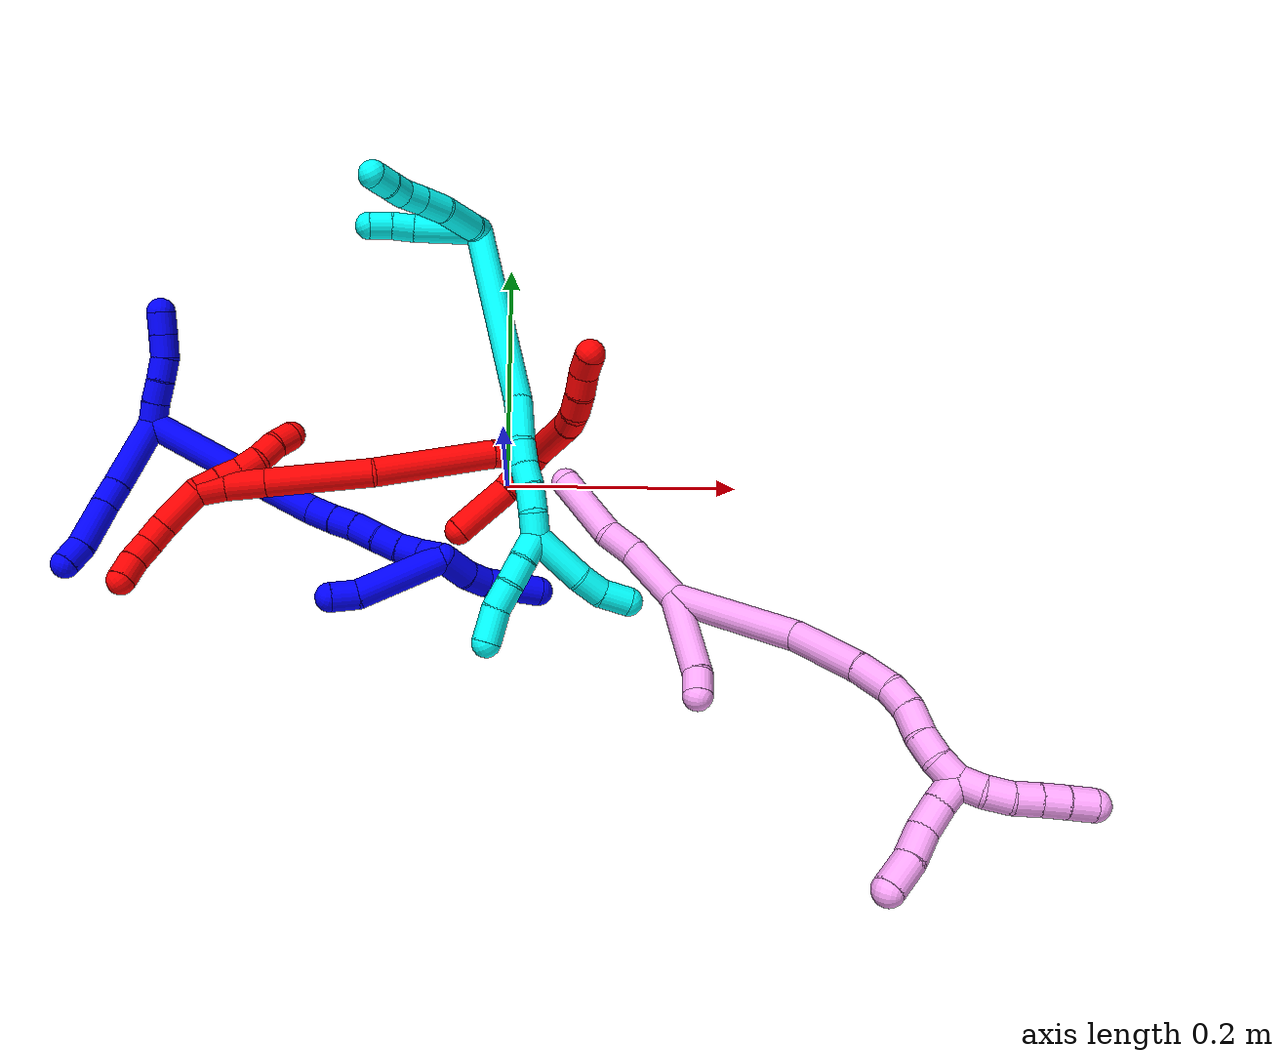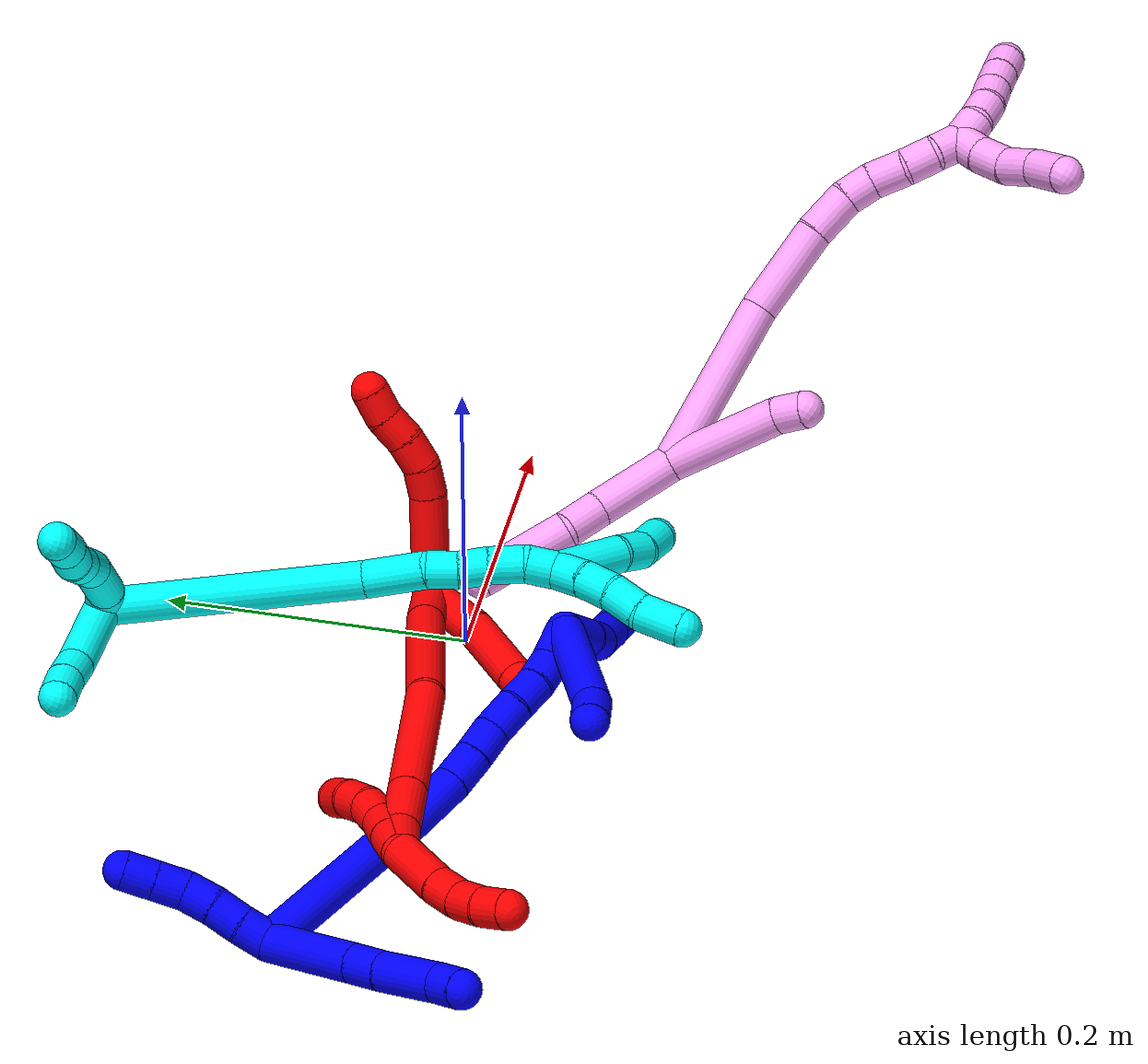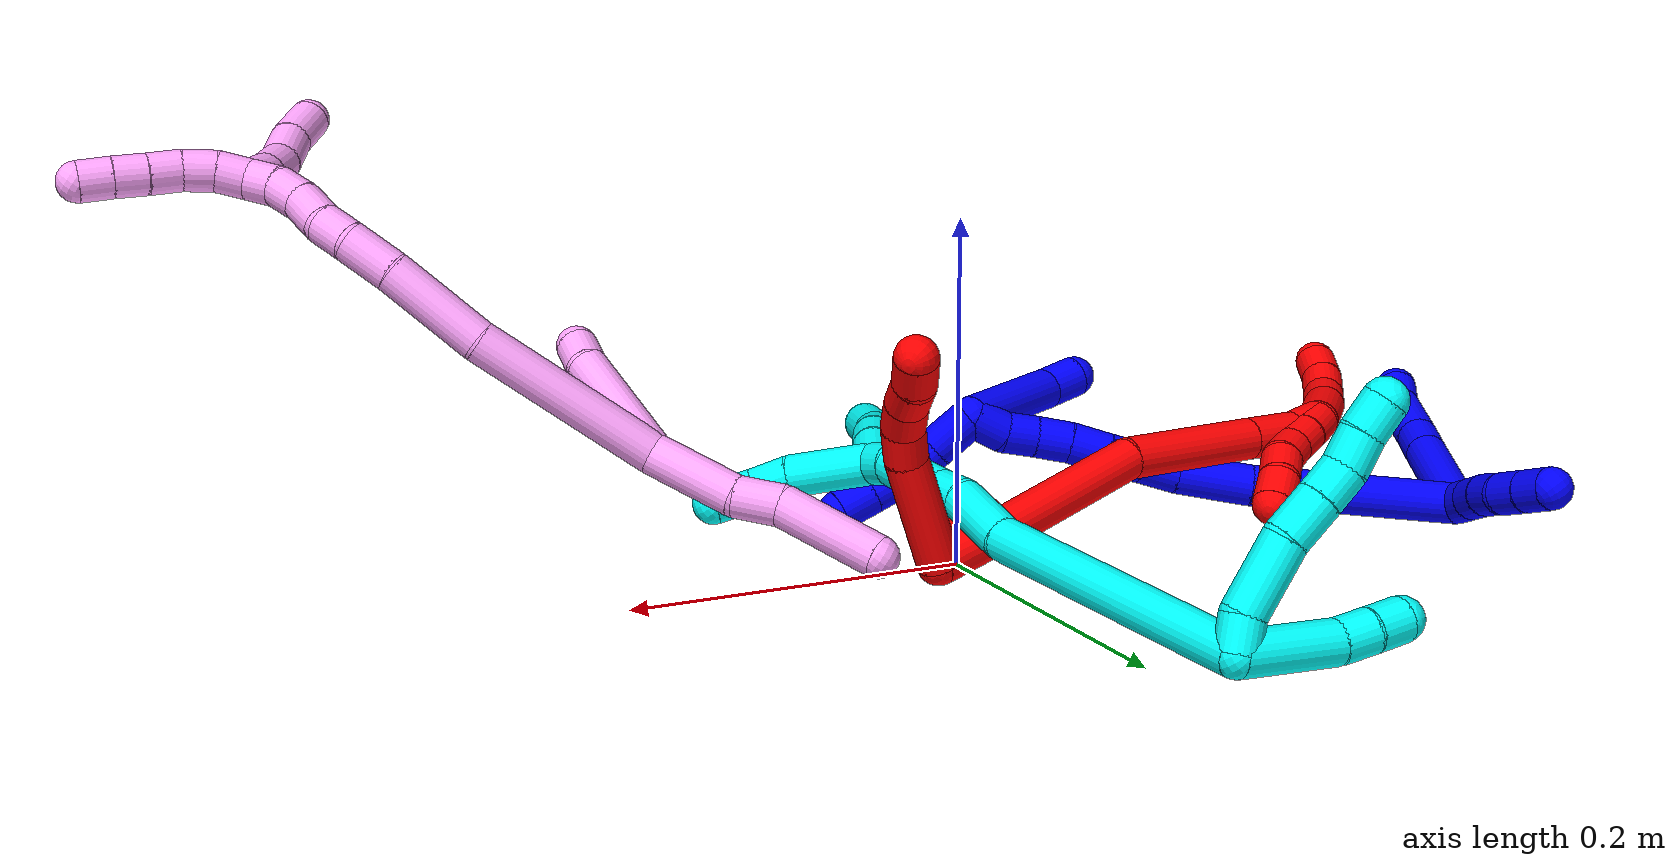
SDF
<sdf version="1.7">
 <world name="default">
  <plugin name="TubeGeneratorPlugin" filename="libtube_generator_plugin.so"/>
  <model name="photoneo_s_sensor">
   <static>1</static>
   <pose>0 0 2 1.57079 1.57079 3.14159</pose>
   <link name="link">
    <inertial><mass>0.1</mass></inertial>
    <sensor name="sensor" type="depth">
     <update_rate>30</update_rate>
     <camera>
      <horizontal_fov>1.22</horizontal_fov>
      <image><width>1920</width><height>1200</height><format>B8G8R8</format></image>
      <clip><near>0.1</near><far>4</far></clip>
      <depth_camera><output>points</output></depth_camera>
     </camera>
     <plugin name="camera_plugin" filename="libgazebo_ros_depth_camera.so">
      <baseline>0.2</baseline>
      <alwaysOn>1</alwaysOn>
      <updateRate>0.0</updateRate>
      <cameraName>camera_ir</cameraName>
      <imageTopicName>/camera/color/image_raw</imageTopicName>
      <cameraInfoTopicName>/camera/color/camera_info</cameraInfoTopicName>
      <depthImageTopicName>/camera/depth/image_raw</depthImageTopicName>
      <depthImageCameraInfoTopicName>/camera/depth/camera_info</depthImageCameraInfoTopicName>
      <pointCloudTopicName>/camera/depth/points</pointCloudTopicName>
      <frameName>fr_optical</frameName>
      <pointCloudCutoff>0.1</pointCloudCutoff>
      <pointCloudCutoffMax>2.0</pointCloudCutoffMax>
      <distortionK1>0</distortionK1>
      <distortionK2>0</distortionK2>
      <distortionK3>0</distortionK3>
      <distortionT1>0</distortionT1>
      <distortionT2>0</distortionT2>
      <CxPrime>0</CxPrime>
      <Cx>0</Cx>
      <Cy>0</Cy>
      <focalLength>0</focalLength>
      <hackBaseline>0</hackBaseline>
     </plugin>
    </sensor>
   </link>
  </model>
  <gravity>0 0 -9.8</gravity>
  <magnetic_field>6e-06 2.3e-05 -4.2e-05</magnetic_field>
  <atmosphere type="adiabatic"/>
  <physics name="default_physics" default="0" type="ode">
   <max_step_size>0.003</max_step_size>
   <real_time_factor>1</real_time_factor>
   <real_time_update_rate>1000</real_time_update_rate>
   <max_contacts>10000</max_contacts>
   <ode>
    <solver>
     <type>quick</type>
     <iters>100</iters>
     <sor>1.3</sor>
     <use_dynamic_moi_rescaling>0</use_dynamic_moi_rescaling>
    </solver>
    <constraints>
     <contact_max_correcting_vel>0</contact_max_correcting_vel>
     <contact_surface_layer>0.001</contact_surface_layer>
     <cfm>0</cfm>
     <erp>0.2</erp>
    </constraints>
   </ode>
  </physics>
  <scene><ambient>0.4 0.4 0.4 1</ambient><background>0.7 0.7 0.7 1</background><shadows>0</shadows></scene>
  <audio><device>default</device></audio>
  <spherical_coordinates>
   <surface_model>EARTH_WGS84</surface_model>
   <latitude_deg>0</latitude_deg>
   <longitude_deg>0</longitude_deg>
   <elevation>0</elevation>
   <heading_deg>0</heading_deg>
  </spherical_coordinates>
  <model name="bin">
   <static>1</static>
   <link name="bottom">
    <collision name="collision-bottom">
     <pose>0 0 -0.01 0 -0 0</pose>
     <geometry><box><size>0.8 0.6 0.02</size></box></geometry>
     <surface>
      <friction><ode><mu>100</mu><mu2>100</mu2></ode></friction>
      <contact><collide_bitmask>65535</collide_bitmask></contact>
     </surface>
    </collision>
   </link>
   <link name="west_wall">
    <collision name="collision-west_wall">
     <pose>-0.41 0 0.1 0 -0 0</pose>
     <geometry><box><size>0.02 0.6 0.2</size></box></geometry>
     <surface>
      <friction><ode><mu>100</mu><mu2>100</mu2></ode></friction>
      <contact><collide_bitmask>65535</collide_bitmask></contact>
     </surface>
    </collision>
   </link>
   <link name="east_wall">
    <collision name="collision-east_wall">
     <pose>0.41 0 0.1 0 -0 0</pose>
     <geometry><box><size>0.02 0.6 0.2</size></box></geometry>
     <surface>
      <friction><ode><mu>100</mu><mu2>100</mu2></ode></friction>
      <contact><collide_bitmask>65535</collide_bitmask></contact>
     </surface>
    </collision>
   </link>
   <link name="south_wall">
    <collision name="collision-south_wall">
     <pose>0 -0.31 0.1 0 -0 0</pose>
     <geometry><box><size>0.8 0.02 0.2</size></box></geometry>
     <surface>
      <friction><ode><mu>100</mu><mu2>100</mu2></ode></friction>
      <contact><collide_bitmask>65535</collide_bitmask></contact>
     </surface>
    </collision>
   </link>
   <link name="north_wall">
    <collision name="collision-north_wall">
     <pose>0 0.31 0.1 0 -0 0</pose>
     <geometry><box><size>0.8 0.02 0.2</size></box></geometry>
     <surface>
      <friction><ode><mu>100</mu><mu2>100</mu2></ode></friction>
      <contact><collide_bitmask>65535</collide_bitmask></contact>
     </surface>
    </collision>
   </link>
  </model>
  <model name="1">
   <static>0</static>
   <link name="1">
    <collision name="collision-cylinder-e_1_2_8">
     <pose>0.00879 -0.029521 0.011271 1.20609 0.271308 0.18743</pose>
     <geometry><cylinder><radius>0.0125</radius><length>0.065599</length></cylinder></geometry>
     <surface>
      <friction><ode><mu>1.16</mu><mu2>1.16</mu2><slip1>0</slip1><slip2>0</slip2></ode></friction>
      <contact><ode><kp>1e+06</kp><kd>1</kd><max_vel>0</max_vel><min_depth>0.001</min_depth></ode></contact>
     </surface>
    </collision>
    <visual name="visual-cylinder-e_1_2_8">
     <pose>0.00879 -0.029521 0.011271 1.20609 0.271308 0.18743</pose>
     <geometry><cylinder><radius>0.0125</radius><length>0.065599</length></cylinder></geometry>
     <material><ambient>0 0 1 1</ambient></material>
    </visual>
    <collision name="collision-cylinder-e_2_8_9">
     <pose>0.020457 -0.068949 0.026551 1.18622 0.262994 0.177836</pose>
     <geometry><cylinder><radius>0.0125</radius><length>0.022135</length></cylinder></geometry>
     <surface>
      <friction><ode><mu>1.16</mu><mu2>1.16</mu2><slip1>0</slip1><slip2>0</slip2></ode></friction>
      <contact><ode><kp>1e+06</kp><kd>1</kd><max_vel>0</max_vel><min_depth>0.001</min_depth></ode></contact>
     </surface>
    </collision>
    <visual name="visual-cylinder-e_2_8_9">
     <pose>0.020457 -0.068949 0.026551 1.18622 0.262994 0.177836</pose>
     <geometry><cylinder><radius>0.0125</radius><length>0.022135</length></cylinder></geometry>
     <material><ambient>0 0 1 1</ambient></material>
    </visual>
    <collision name="collision-cylinder-e_3_9_10">
     <pose>0.029669 -0.097471 0.037573 1.21057 0.308271 0.214183</pose>
     <geometry><cylinder><radius>0.0125</radius><length>0.041754</length></cylinder></geometry>
     <surface>
      <friction><ode><mu>1.16</mu><mu2>1.16</mu2><slip1>0</slip1><slip2>0</slip2></ode></friction>
      <contact><ode><kp>1e+06</kp><kd>1</kd><max_vel>0</max_vel><min_depth>0.001</min_depth></ode></contact>
     </surface>
    </collision>
    <visual name="visual-cylinder-e_3_9_10">
     <pose>0.029669 -0.097471 0.037573 1.21057 0.308271 0.214183</pose>
     <geometry><cylinder><radius>0.0125</radius><length>0.041754</length></cylinder></geometry>
     <material><ambient>0 0 1 1</ambient></material>
    </visual>
    <collision name="collision-cylinder-e_4_10_6">
     <pose>0.038925 -0.124275 0.050026 0.984273 0.288855 0.155636</pose>
     <geometry><cylinder><radius>0.0125</radius><length>0.020512</length></cylinder></geometry>
     <surface>
      <friction><ode><mu>1.16</mu><mu2>1.16</mu2><slip1>0</slip1><slip2>0</slip2></ode></friction>
      <contact><ode><kp>1e+06</kp><kd>1</kd><max_vel>0</max_vel><min_depth>0.001</min_depth></ode></contact>
     </surface>
    </collision>
    <visual name="visual-cylinder-e_4_10_6">
     <pose>0.038925 -0.124275 0.050026 0.984273 0.288855 0.155636</pose>
     <geometry><cylinder><radius>0.0125</radius><length>0.020512</length></cylinder></geometry>
     <material><ambient>0 0 1 1</ambient></material>
    </visual>
    <collision name="collision-cylinder-e_1_2_11">
     <pose>0.001498 0.009784 0.001422 -1.42652 0.150412 -0.1302</pose>
     <geometry><cylinder><radius>0.0125</radius><length>0.02</length></cylinder></geometry>
     <surface>
      <friction><ode><mu>1.16</mu><mu2>1.16</mu2><slip1>0</slip1><slip2>0</slip2></ode></friction>
      <contact><ode><kp>1e+06</kp><kd>1</kd><max_vel>0</max_vel><min_depth>0.001</min_depth></ode></contact>
     </surface>
    </collision>
    <visual name="visual-cylinder-e_1_2_11">
     <pose>0.001498 0.009784 0.001422 -1.42652 0.150412 -0.1302</pose>
     <geometry><cylinder><radius>0.0125</radius><length>0.02</length></cylinder></geometry>
     <material><ambient>0 0 1 1</ambient></material>
    </visual>
    <collision name="collision-cylinder-e_2_11_12">
     <pose>0.0049 0.029368 0.003437 -1.5103 0.191526 -0.180339</pose>
     <geometry><cylinder><radius>0.0125</radius><length>0.02</length></cylinder></geometry>
     <surface>
      <friction><ode><mu>1.16</mu><mu2>1.16</mu2><slip1>0</slip1><slip2>0</slip2></ode></friction>
      <contact><ode><kp>1e+06</kp><kd>1</kd><max_vel>0</max_vel><min_depth>0.001</min_depth></ode></contact>
     </surface>
    </collision>
    <visual name="visual-cylinder-e_2_11_12">
     <pose>0.0049 0.029368 0.003437 -1.5103 0.191526 -0.180339</pose>
     <geometry><cylinder><radius>0.0125</radius><length>0.02</length></cylinder></geometry>
     <material><ambient>0 0 1 1</ambient></material>
    </visual>
    <collision name="collision-cylinder-e_3_12_13">
     <pose>0.007578 0.049117 0.004664 -1.50715 0.077451 -0.072677</pose>
     <geometry><cylinder><radius>0.0125</radius><length>0.02</length></cylinder></geometry>
     <surface>
      <friction><ode><mu>1.16</mu><mu2>1.16</mu2><slip1>0</slip1><slip2>0</slip2></ode></friction>
      <contact><ode><kp>1e+06</kp><kd>1</kd><max_vel>0</max_vel><min_depth>0.001</min_depth></ode></contact>
     </surface>
    </collision>
    <visual name="visual-cylinder-e_3_12_13">
     <pose>0.007578 0.049117 0.004664 -1.50715 0.077451 -0.072677</pose>
     <geometry><cylinder><radius>0.0125</radius><length>0.02</length></cylinder></geometry>
     <material><ambient>0 0 1 1</ambient></material>
    </visual>
    <collision name="collision-cylinder-e_4_13_14">
     <pose>0.007994 0.068596 0.00831 -1.26467 -0.035761 0.026204</pose>
     <geometry><cylinder><radius>0.0125</radius><length>0.02</length></cylinder></geometry>
     <surface>
      <friction><ode><mu>1.16</mu><mu2>1.16</mu2><slip1>0</slip1><slip2>0</slip2></ode></friction>
      <contact><ode><kp>1e+06</kp><kd>1</kd><max_vel>0</max_vel><min_depth>0.001</min_depth></ode></contact>
     </surface>
    </collision>
    <visual name="visual-cylinder-e_4_13_14">
     <pose>0.007994 0.068596 0.00831 -1.26467 -0.035761 0.026204</pose>
     <geometry><cylinder><radius>0.0125</radius><length>0.02</length></cylinder></geometry>
     <material><ambient>0 0 1 1</ambient></material>
    </visual>
    <collision name="collision-cylinder-e_5_14_5">
     <pose>0.00728 0.087603 0.01449 -1.24819 -0.035613 0.025646</pose>
     <geometry><cylinder><radius>0.0125</radius><length>0.02</length></cylinder></geometry>
     <surface>
      <friction><ode><mu>1.16</mu><mu2>1.16</mu2><slip1>0</slip1><slip2>0</slip2></ode></friction>
      <contact><ode><kp>1e+06</kp><kd>1</kd><max_vel>0</max_vel><min_depth>0.001</min_depth></ode></contact>
     </surface>
    </collision>
    <visual name="visual-cylinder-e_5_14_5">
     <pose>0.00728 0.087603 0.01449 -1.24819 -0.035613 0.025646</pose>
     <geometry><cylinder><radius>0.0125</radius><length>0.02</length></cylinder></geometry>
     <material><ambient>0 0 1 1</ambient></material>
    </visual>
    <collision name="collision-cylinder-e_1_2_15">
     <pose>0.037294 -0.015691 -0.046566 2.81657 0.649205 2.23483</pose>
     <geometry><cylinder><radius>0.0125</radius><length>0.123377</length></cylinder></geometry>
     <surface>
      <friction><ode><mu>1.16</mu><mu2>1.16</mu2><slip1>0</slip1><slip2>0</slip2></ode></friction>
      <contact><ode><kp>1e+06</kp><kd>1</kd><max_vel>0</max_vel><min_depth>0.001</min_depth></ode></contact>
     </surface>
    </collision>
    <visual name="visual-cylinder-e_1_2_15">
     <pose>0.037294 -0.015691 -0.046566 2.81657 0.649205 2.23483</pose>
     <geometry><cylinder><radius>0.0125</radius><length>0.123377</length></cylinder></geometry>
     <material><ambient>0 0 1 1</ambient></material>
    </visual>
    <collision name="collision-cylinder-e_2_15_16">
     <pose>0.089651 -0.03669 -0.109019 2.81918 0.732435 2.33953</pose>
     <geometry><cylinder><radius>0.0125</radius><length>0.045053</length></cylinder></geometry>
     <surface>
      <friction><ode><mu>1.16</mu><mu2>1.16</mu2><slip1>0</slip1><slip2>0</slip2></ode></friction>
      <contact><ode><kp>1e+06</kp><kd>1</kd><max_vel>0</max_vel><min_depth>0.001</min_depth></ode></contact>
     </surface>
    </collision>
    <visual name="visual-cylinder-e_2_15_16">
     <pose>0.089651 -0.03669 -0.109019 2.81918 0.732435 2.33953</pose>
     <geometry><cylinder><radius>0.0125</radius><length>0.045053</length></cylinder></geometry>
     <material><ambient>0 0 1 1</ambient></material>
    </visual>
    <collision name="collision-cylinder-e_3_16_17">
     <pose>0.113462 -0.04369 -0.1323 2.91651 0.856377 2.65613</pose>
     <geometry><cylinder><radius>0.0125</radius><length>0.023157</length></cylinder></geometry>
     <surface>
      <friction><ode><mu>1.16</mu><mu2>1.16</mu2><slip1>0</slip1><slip2>0</slip2></ode></friction>
      <contact><ode><kp>1e+06</kp><kd>1</kd><max_vel>0</max_vel><min_depth>0.001</min_depth></ode></contact>
     </surface>
    </collision>
    <visual name="visual-cylinder-e_3_16_17">
     <pose>0.113462 -0.04369 -0.1323 2.91651 0.856377 2.65613</pose>
     <geometry><cylinder><radius>0.0125</radius><length>0.023157</length></cylinder></geometry>
     <material><ambient>0 0 1 1</ambient></material>
    </visual>
    <collision name="collision-cylinder-e_4_17_18">
     <pose>0.130121 -0.04637 -0.146748 3.00256 0.837878 2.83137</pose>
     <geometry><cylinder><radius>0.0125</radius><length>0.021291</length></cylinder></geometry>
     <surface>
      <friction><ode><mu>1.16</mu><mu2>1.16</mu2><slip1>0</slip1><slip2>0</slip2></ode></friction>
      <contact><ode><kp>1e+06</kp><kd>1</kd><max_vel>0</max_vel><min_depth>0.001</min_depth></ode></contact>
     </surface>
    </collision>
    <visual name="visual-cylinder-e_4_17_18">
     <pose>0.130121 -0.04637 -0.146748 3.00256 0.837878 2.83137</pose>
     <geometry><cylinder><radius>0.0125</radius><length>0.021291</length></cylinder></geometry>
     <material><ambient>0 0 1 1</ambient></material>
    </visual>
    <collision name="collision-cylinder-e_5_18_19">
     <pose>0.146977 -0.049748 -0.161086 2.82449 0.862193 2.47246</pose>
     <geometry><cylinder><radius>0.0125</radius><length>0.02356</length></cylinder></geometry>
     <surface>
      <friction><ode><mu>1.16</mu><mu2>1.16</mu2><slip1>0</slip1><slip2>0</slip2></ode></friction>
      <contact><ode><kp>1e+06</kp><kd>1</kd><max_vel>0</max_vel><min_depth>0.001</min_depth></ode></contact>
     </surface>
    </collision>
    <visual name="visual-cylinder-e_5_18_19">
     <pose>0.146977 -0.049748 -0.161086 2.82449 0.862193 2.47246</pose>
     <geometry><cylinder><radius>0.0125</radius><length>0.02356</length></cylinder></geometry>
     <material><ambient>0 0 1 1</ambient></material>
    </visual>
    <collision name="collision-cylinder-e_6_19_20">
     <pose>0.163181 -0.054136 -0.175942 2.88367 0.747574 2.50295</pose>
     <geometry><cylinder><radius>0.0125</radius><length>0.021357</length></cylinder></geometry>
     <surface>
      <friction><ode><mu>1.16</mu><mu2>1.16</mu2><slip1>0</slip1><slip2>0</slip2></ode></friction>
      <contact><ode><kp>1e+06</kp><kd>1</kd><max_vel>0</max_vel><min_depth>0.001</min_depth></ode></contact>
     </surface>
    </collision>
    <visual name="visual-cylinder-e_6_19_20">
     <pose>0.163181 -0.054136 -0.175942 2.88367 0.747574 2.50295</pose>
     <geometry><cylinder><radius>0.0125</radius><length>0.021357</length></cylinder></geometry>
     <material><ambient>0 0 1 1</ambient></material>
    </visual>
    <collision name="collision-cylinder-e_7_20_21">
     <pose>0.17722 -0.056392 -0.191031 3.10723 0.733488 3.05218</pose>
     <geometry><cylinder><radius>0.0125</radius><length>0.020251</length></cylinder></geometry>
     <surface>
      <friction><ode><mu>1.16</mu><mu2>1.16</mu2><slip1>0</slip1><slip2>0</slip2></ode></friction>
      <contact><ode><kp>1e+06</kp><kd>1</kd><max_vel>0</max_vel><min_depth>0.001</min_depth></ode></contact>
     </surface>
    </collision>
    <visual name="visual-cylinder-e_7_20_21">
     <pose>0.17722 -0.056392 -0.191031 3.10723 0.733488 3.05218</pose>
     <geometry><cylinder><radius>0.0125</radius><length>0.020251</length></cylinder></geometry>
     <material><ambient>0 0 1 1</ambient></material>
    </visual>
    <collision name="collision-cylinder-e_8_21_1">
     <pose>0.193423 -0.05614 -0.204152 -3.05081 1.03255 -2.98188</pose>
     <geometry><cylinder><radius>0.0125</radius><length>0.021954</length></cylinder></geometry>
     <surface>
      <friction><ode><mu>1.16</mu><mu2>1.16</mu2><slip1>0</slip1><slip2>0</slip2></ode></friction>
      <contact><ode><kp>1e+06</kp><kd>1</kd><max_vel>0</max_vel><min_depth>0.001</min_depth></ode></contact>
     </surface>
    </collision>
    <visual name="visual-cylinder-e_8_21_1">
     <pose>0.193423 -0.05614 -0.204152 -3.05081 1.03255 -2.98188</pose>
     <geometry><cylinder><radius>0.0125</radius><length>0.021954</length></cylinder></geometry>
     <material><ambient>0 0 1 1</ambient></material>
    </visual>
    <collision name="collision-cylinder-e_1_1_22">
     <pose>0.192288 -0.078204 -0.180564 0.658257 -0.278716 -0.095744</pose>
     <geometry><cylinder><radius>0.0125</radius><length>0.076766</length></cylinder></geometry>
     <surface>
      <friction><ode><mu>1.16</mu><mu2>1.16</mu2><slip1>0</slip1><slip2>0</slip2></ode></friction>
      <contact><ode><kp>1e+06</kp><kd>1</kd><max_vel>0</max_vel><min_depth>0.001</min_depth></ode></contact>
     </surface>
    </collision>
    <visual name="visual-cylinder-e_1_1_22">
     <pose>0.192288 -0.078204 -0.180564 0.658257 -0.278716 -0.095744</pose>
     <geometry><cylinder><radius>0.0125</radius><length>0.076766</length></cylinder></geometry>
     <material><ambient>0 0 1 1</ambient></material>
    </visual>
    <collision name="collision-cylinder-e_2_22_4">
     <pose>0.178997 -0.104304 -0.140646 0.317531 -0.237295 -0.038169</pose>
     <geometry><cylinder><radius>0.0125</radius><length>0.023234</length></cylinder></geometry>
     <surface>
      <friction><ode><mu>1.16</mu><mu2>1.16</mu2><slip1>0</slip1><slip2>0</slip2></ode></friction>
      <contact><ode><kp>1e+06</kp><kd>1</kd><max_vel>0</max_vel><min_depth>0.001</min_depth></ode></contact>
     </surface>
    </collision>
    <visual name="visual-cylinder-e_2_22_4">
     <pose>0.178997 -0.104304 -0.140646 0.317531 -0.237295 -0.038169</pose>
     <geometry><cylinder><radius>0.0125</radius><length>0.023234</length></cylinder></geometry>
     <material><ambient>0 0 1 1</ambient></material>
    </visual>
    <collision name="collision-cylinder-e_1_1_23">
     <pose>0.200475 -0.060515 -0.223459 2.79916 -0.161732 -0.876604</pose>
     <geometry><cylinder><radius>0.0125</radius><length>0.029481</length></cylinder></geometry>
     <surface>
      <friction><ode><mu>1.16</mu><mu2>1.16</mu2><slip1>0</slip1><slip2>0</slip2></ode></friction>
      <contact><ode><kp>1e+06</kp><kd>1</kd><max_vel>0</max_vel><min_depth>0.001</min_depth></ode></contact>
     </surface>
    </collision>
    <visual name="visual-cylinder-e_1_1_23">
     <pose>0.200475 -0.060515 -0.223459 2.79916 -0.161732 -0.876604</pose>
     <geometry><cylinder><radius>0.0125</radius><length>0.029481</length></cylinder></geometry>
     <material><ambient>0 0 1 1</ambient></material>
    </visual>
    <collision name="collision-cylinder-e_2_23_24">
     <pose>0.196259 -0.066924 -0.247211 2.99103 -0.179304 -1.74542</pose>
     <geometry><cylinder><radius>0.0125</radius><length>0.020657</length></cylinder></geometry>
     <surface>
      <friction><ode><mu>1.16</mu><mu2>1.16</mu2><slip1>0</slip1><slip2>0</slip2></ode></friction>
      <contact><ode><kp>1e+06</kp><kd>1</kd><max_vel>0</max_vel><min_depth>0.001</min_depth></ode></contact>
     </surface>
    </collision>
    <visual name="visual-cylinder-e_2_23_24">
     <pose>0.196259 -0.066924 -0.247211 2.99103 -0.179304 -1.74542</pose>
     <geometry><cylinder><radius>0.0125</radius><length>0.020657</length></cylinder></geometry>
     <material><ambient>0 0 1 1</ambient></material>
    </visual>
    <collision name="collision-cylinder-e_3_24_25">
     <pose>0.195934 -0.067838 -0.271107 -3.09755 0.109018 -2.37421</pose>
     <geometry><cylinder><radius>0.0125</radius><length>0.027887</length></cylinder></geometry>
     <surface>
      <friction><ode><mu>1.16</mu><mu2>1.16</mu2><slip1>0</slip1><slip2>0</slip2></ode></friction>
      <contact><ode><kp>1e+06</kp><kd>1</kd><max_vel>0</max_vel><min_depth>0.001</min_depth></ode></contact>
     </surface>
    </collision>
    <visual name="visual-cylinder-e_3_24_25">
     <pose>0.195934 -0.067838 -0.271107 -3.09755 0.109018 -2.37421</pose>
     <geometry><cylinder><radius>0.0125</radius><length>0.027887</length></cylinder></geometry>
     <material><ambient>0 0 1 1</ambient></material>
    </visual>
    <collision name="collision-cylinder-e_4_25_3">
     <pose>0.198804 -0.066614 -0.29584 -3.08521 0.123453 -2.28552</pose>
     <geometry><cylinder><radius>0.0125</radius><length>0.021974</length></cylinder></geometry>
     <surface>
      <friction><ode><mu>1.16</mu><mu2>1.16</mu2><slip1>0</slip1><slip2>0</slip2></ode></friction>
      <contact><ode><kp>1e+06</kp><kd>1</kd><max_vel>0</max_vel><min_depth>0.001</min_depth></ode></contact>
     </surface>
    </collision>
    <visual name="visual-cylinder-e_4_25_3">
     <pose>0.198804 -0.066614 -0.29584 -3.08521 0.123453 -2.28552</pose>
     <geometry><cylinder><radius>0.0125</radius><length>0.021974</length></cylinder></geometry>
     <material><ambient>0 0 1 1</ambient></material>
    </visual>
    <collision name="collision-sphere-3">
     <pose>0.200157 -0.065999 -0.306726 0 -0 0</pose>
     <geometry><sphere><radius>0.0125</radius></sphere></geometry>
     <surface>
      <friction><ode><mu>1.16</mu><mu2>1.16</mu2><slip1>0</slip1><slip2>0</slip2></ode></friction>
      <contact><ode><kp>1e+06</kp><kd>1</kd><max_vel>0</max_vel><min_depth>0.001</min_depth></ode></contact>
     </surface>
    </collision>
    <visual name="visual-sphere-3">
     <pose>0.200157 -0.065999 -0.306726 0 -0 0</pose>
     <geometry><sphere><radius>0.0125</radius></sphere></geometry>
     <material><ambient>0 0 1 1</ambient></material>
    </visual>
    <collision name="collision-sphere-25">
     <pose>0.197451 -0.067228 -0.284954 0 -0 0</pose>
     <geometry><sphere><radius>0.0125</radius></sphere></geometry>
     <surface>
      <friction><ode><mu>1.16</mu><mu2>1.16</mu2><slip1>0</slip1><slip2>0</slip2></ode></friction>
      <contact><ode><kp>1e+06</kp><kd>1</kd><max_vel>0</max_vel><min_depth>0.001</min_depth></ode></contact>
     </surface>
    </collision>
    <visual name="visual-sphere-25">
     <pose>0.197451 -0.067228 -0.284954 0 -0 0</pose>
     <geometry><sphere><radius>0.0125</radius></sphere></geometry>
     <material><ambient>0 0 1 1</ambient></material>
    </visual>
    <collision name="collision-sphere-24">
     <pose>0.194417 -0.068449 -0.257259 0 -0 0</pose>
     <geometry><sphere><radius>0.0125</radius></sphere></geometry>
     <surface>
      <friction><ode><mu>1.16</mu><mu2>1.16</mu2><slip1>0</slip1><slip2>0</slip2></ode></friction>
      <contact><ode><kp>1e+06</kp><kd>1</kd><max_vel>0</max_vel><min_depth>0.001</min_depth></ode></contact>
     </surface>
    </collision>
    <visual name="visual-sphere-24">
     <pose>0.194417 -0.068449 -0.257259 0 -0 0</pose>
     <geometry><sphere><radius>0.0125</radius></sphere></geometry>
     <material><ambient>0 0 1 1</ambient></material>
    </visual>
    <collision name="collision-sphere-23">
     <pose>0.198101 -0.0654 -0.237163 0 -0 0</pose>
     <geometry><sphere><radius>0.0125</radius></sphere></geometry>
     <surface>
      <friction><ode><mu>1.16</mu><mu2>1.16</mu2><slip1>0</slip1><slip2>0</slip2></ode></friction>
      <contact><ode><kp>1e+06</kp><kd>1</kd><max_vel>0</max_vel><min_depth>0.001</min_depth></ode></contact>
     </surface>
    </collision>
    <visual name="visual-sphere-23">
     <pose>0.198101 -0.0654 -0.237163 0 -0 0</pose>
     <geometry><sphere><radius>0.0125</radius></sphere></geometry>
     <material><ambient>0 0 1 1</ambient></material>
    </visual>
    <collision name="collision-sphere-4">
     <pose>0.176267 -0.107829 -0.129919 0 -0 0</pose>
     <geometry><sphere><radius>0.0125</radius></sphere></geometry>
     <surface>
      <friction><ode><mu>1.16</mu><mu2>1.16</mu2><slip1>0</slip1><slip2>0</slip2></ode></friction>
      <contact><ode><kp>1e+06</kp><kd>1</kd><max_vel>0</max_vel><min_depth>0.001</min_depth></ode></contact>
     </surface>
    </collision>
    <visual name="visual-sphere-4">
     <pose>0.176267 -0.107829 -0.129919 0 -0 0</pose>
     <geometry><sphere><radius>0.0125</radius></sphere></geometry>
     <material><ambient>0 0 1 1</ambient></material>
    </visual>
    <collision name="collision-sphere-22">
     <pose>0.181728 -0.100778 -0.151373 0 -0 0</pose>
     <geometry><sphere><radius>0.0125</radius></sphere></geometry>
     <surface>
      <friction><ode><mu>1.16</mu><mu2>1.16</mu2><slip1>0</slip1><slip2>0</slip2></ode></friction>
      <contact><ode><kp>1e+06</kp><kd>1</kd><max_vel>0</max_vel><min_depth>0.001</min_depth></ode></contact>
     </surface>
    </collision>
    <visual name="visual-sphere-22">
     <pose>0.181728 -0.100778 -0.151373 0 -0 0</pose>
     <geometry><sphere><radius>0.0125</radius></sphere></geometry>
     <material><ambient>0 0 1 1</ambient></material>
    </visual>
    <collision name="collision-sphere-1">
     <pose>0.202848 -0.05563 -0.209756 0 -0 0</pose>
     <geometry><sphere><radius>0.0125</radius></sphere></geometry>
     <surface>
      <friction><ode><mu>1.16</mu><mu2>1.16</mu2><slip1>0</slip1><slip2>0</slip2></ode></friction>
      <contact><ode><kp>1e+06</kp><kd>1</kd><max_vel>0</max_vel><min_depth>0.001</min_depth></ode></contact>
     </surface>
    </collision>
    <visual name="visual-sphere-1">
     <pose>0.202848 -0.05563 -0.209756 0 -0 0</pose>
     <geometry><sphere><radius>0.0125</radius></sphere></geometry>
     <material><ambient>0 0 1 1</ambient></material>
    </visual>
    <collision name="collision-sphere-21">
     <pose>0.183998 -0.05665 -0.198548 0 -0 0</pose>
     <geometry><sphere><radius>0.0125</radius></sphere></geometry>
     <surface>
      <friction><ode><mu>1.16</mu><mu2>1.16</mu2><slip1>0</slip1><slip2>0</slip2></ode></friction>
      <contact><ode><kp>1e+06</kp><kd>1</kd><max_vel>0</max_vel><min_depth>0.001</min_depth></ode></contact>
     </surface>
    </collision>
    <visual name="visual-sphere-21">
     <pose>0.183998 -0.05665 -0.198548 0 -0 0</pose>
     <geometry><sphere><radius>0.0125</radius></sphere></geometry>
     <material><ambient>0 0 1 1</ambient></material>
    </visual>
    <collision name="collision-sphere-11">
     <pose>0.002997 0.019569 0.002843 0 -0 0</pose>
     <geometry><sphere><radius>0.0125</radius></sphere></geometry>
     <surface>
      <friction><ode><mu>1.16</mu><mu2>1.16</mu2><slip1>0</slip1><slip2>0</slip2></ode></friction>
      <contact><ode><kp>1e+06</kp><kd>1</kd><max_vel>0</max_vel><min_depth>0.001</min_depth></ode></contact>
     </surface>
    </collision>
    <visual name="visual-sphere-11">
     <pose>0.002997 0.019569 0.002843 0 -0 0</pose>
     <geometry><sphere><radius>0.0125</radius></sphere></geometry>
     <material><ambient>0 0 1 1</ambient></material>
    </visual>
    <collision name="collision-sphere-6">
     <pose>0.041846 -0.132463 0.055467 0 -0 0</pose>
     <geometry><sphere><radius>0.0125</radius></sphere></geometry>
     <surface>
      <friction><ode><mu>1.16</mu><mu2>1.16</mu2><slip1>0</slip1><slip2>0</slip2></ode></friction>
      <contact><ode><kp>1e+06</kp><kd>1</kd><max_vel>0</max_vel><min_depth>0.001</min_depth></ode></contact>
     </surface>
    </collision>
    <visual name="visual-sphere-6">
     <pose>0.041846 -0.132463 0.055467 0 -0 0</pose>
     <geometry><sphere><radius>0.0125</radius></sphere></geometry>
     <material><ambient>0 0 1 1</ambient></material>
    </visual>
    <collision name="collision-sphere-10">
     <pose>0.036003 -0.116087 0.044584 0 -0 0</pose>
     <geometry><sphere><radius>0.0125</radius></sphere></geometry>
     <surface>
      <friction><ode><mu>1.16</mu><mu2>1.16</mu2><slip1>0</slip1><slip2>0</slip2></ode></friction>
      <contact><ode><kp>1e+06</kp><kd>1</kd><max_vel>0</max_vel><min_depth>0.001</min_depth></ode></contact>
     </surface>
    </collision>
    <visual name="visual-sphere-10">
     <pose>0.036003 -0.116087 0.044584 0 -0 0</pose>
     <geometry><sphere><radius>0.0125</radius></sphere></geometry>
     <material><ambient>0 0 1 1</ambient></material>
    </visual>
    <collision name="collision-sphere-9">
     <pose>0.023334 -0.078855 0.030561 0 -0 0</pose>
     <geometry><sphere><radius>0.0125</radius></sphere></geometry>
     <surface>
      <friction><ode><mu>1.16</mu><mu2>1.16</mu2><slip1>0</slip1><slip2>0</slip2></ode></friction>
      <contact><ode><kp>1e+06</kp><kd>1</kd><max_vel>0</max_vel><min_depth>0.001</min_depth></ode></contact>
     </surface>
    </collision>
    <visual name="visual-sphere-9">
     <pose>0.023334 -0.078855 0.030561 0 -0 0</pose>
     <geometry><sphere><radius>0.0125</radius></sphere></geometry>
     <material><ambient>0 0 1 1</ambient></material>
    </visual>
    <collision name="collision-sphere-2">
     <geometry><sphere><radius>0.0125</radius></sphere></geometry>
     <surface>
      <friction><ode><mu>1.16</mu><mu2>1.16</mu2><slip1>0</slip1><slip2>0</slip2></ode></friction>
      <contact><ode><kp>1e+06</kp><kd>1</kd><max_vel>0</max_vel><min_depth>0.001</min_depth></ode></contact>
     </surface>
    </collision>
    <visual name="visual-sphere-2">
     <geometry><sphere><radius>0.0125</radius></sphere></geometry>
     <material><ambient>0 0 1 1</ambient></material>
    </visual>
    <collision name="collision-sphere-19">
     <pose>0.155921 -0.052138 -0.16837 0 -0 0</pose>
     <geometry><sphere><radius>0.0125</radius></sphere></geometry>
     <surface>
      <friction><ode><mu>1.16</mu><mu2>1.16</mu2><slip1>0</slip1><slip2>0</slip2></ode></friction>
      <contact><ode><kp>1e+06</kp><kd>1</kd><max_vel>0</max_vel><min_depth>0.001</min_depth></ode></contact>
     </surface>
    </collision>
    <visual name="visual-sphere-19">
     <pose>0.155921 -0.052138 -0.16837 0 -0 0</pose>
     <geometry><sphere><radius>0.0125</radius></sphere></geometry>
     <material><ambient>0 0 1 1</ambient></material>
    </visual>
    <collision name="collision-sphere-8">
     <pose>0.01758 -0.059043 0.022542 0 -0 0</pose>
     <geometry><sphere><radius>0.0125</radius></sphere></geometry>
     <surface>
      <friction><ode><mu>1.16</mu><mu2>1.16</mu2><slip1>0</slip1><slip2>0</slip2></ode></friction>
      <contact><ode><kp>1e+06</kp><kd>1</kd><max_vel>0</max_vel><min_depth>0.001</min_depth></ode></contact>
     </surface>
    </collision>
    <visual name="visual-sphere-8">
     <pose>0.01758 -0.059043 0.022542 0 -0 0</pose>
     <geometry><sphere><radius>0.0125</radius></sphere></geometry>
     <material><ambient>0 0 1 1</ambient></material>
    </visual>
    <collision name="collision-sphere-12">
     <pose>0.006804 0.039167 0.00403 0 -0 0</pose>
     <geometry><sphere><radius>0.0125</radius></sphere></geometry>
     <surface>
      <friction><ode><mu>1.16</mu><mu2>1.16</mu2><slip1>0</slip1><slip2>0</slip2></ode></friction>
      <contact><ode><kp>1e+06</kp><kd>1</kd><max_vel>0</max_vel><min_depth>0.001</min_depth></ode></contact>
     </surface>
    </collision>
    <visual name="visual-sphere-12">
     <pose>0.006804 0.039167 0.00403 0 -0 0</pose>
     <geometry><sphere><radius>0.0125</radius></sphere></geometry>
     <material><ambient>0 0 1 1</ambient></material>
    </visual>
    <collision name="collision-sphere-13">
     <pose>0.008352 0.059067 0.005298 0 -0 0</pose>
     <geometry><sphere><radius>0.0125</radius></sphere></geometry>
     <surface>
      <friction><ode><mu>1.16</mu><mu2>1.16</mu2><slip1>0</slip1><slip2>0</slip2></ode></friction>
      <contact><ode><kp>1e+06</kp><kd>1</kd><max_vel>0</max_vel><min_depth>0.001</min_depth></ode></contact>
     </surface>
    </collision>
    <visual name="visual-sphere-13">
     <pose>0.008352 0.059067 0.005298 0 -0 0</pose>
     <geometry><sphere><radius>0.0125</radius></sphere></geometry>
     <material><ambient>0 0 1 1</ambient></material>
    </visual>
    <collision name="collision-sphere-14">
     <pose>0.007636 0.078125 0.011322 0 -0 0</pose>
     <geometry><sphere><radius>0.0125</radius></sphere></geometry>
     <surface>
      <friction><ode><mu>1.16</mu><mu2>1.16</mu2><slip1>0</slip1><slip2>0</slip2></ode></friction>
      <contact><ode><kp>1e+06</kp><kd>1</kd><max_vel>0</max_vel><min_depth>0.001</min_depth></ode></contact>
     </surface>
    </collision>
    <visual name="visual-sphere-14">
     <pose>0.007636 0.078125 0.011322 0 -0 0</pose>
     <geometry><sphere><radius>0.0125</radius></sphere></geometry>
     <material><ambient>0 0 1 1</ambient></material>
    </visual>
    <collision name="collision-sphere-5">
     <pose>0.006924 0.097081 0.017659 0 -0 0</pose>
     <geometry><sphere><radius>0.0125</radius></sphere></geometry>
     <surface>
      <friction><ode><mu>1.16</mu><mu2>1.16</mu2><slip1>0</slip1><slip2>0</slip2></ode></friction>
      <contact><ode><kp>1e+06</kp><kd>1</kd><max_vel>0</max_vel><min_depth>0.001</min_depth></ode></contact>
     </surface>
    </collision>
    <visual name="visual-sphere-5">
     <pose>0.006924 0.097081 0.017659 0 -0 0</pose>
     <geometry><sphere><radius>0.0125</radius></sphere></geometry>
     <material><ambient>0 0 1 1</ambient></material>
    </visual>
    <collision name="collision-sphere-15">
     <pose>0.074588 -0.031383 -0.093132 0 -0 0</pose>
     <geometry><sphere><radius>0.0125</radius></sphere></geometry>
     <surface>
      <friction><ode><mu>1.16</mu><mu2>1.16</mu2><slip1>0</slip1><slip2>0</slip2></ode></friction>
      <contact><ode><kp>1e+06</kp><kd>1</kd><max_vel>0</max_vel><min_depth>0.001</min_depth></ode></contact>
     </surface>
    </collision>
    <visual name="visual-sphere-15">
     <pose>0.074588 -0.031383 -0.093132 0 -0 0</pose>
     <geometry><sphere><radius>0.0125</radius></sphere></geometry>
     <material><ambient>0 0 1 1</ambient></material>
    </visual>
    <collision name="collision-sphere-16">
     <pose>0.104714 -0.041997 -0.124906 0 -0 0</pose>
     <geometry><sphere><radius>0.0125</radius></sphere></geometry>
     <surface>
      <friction><ode><mu>1.16</mu><mu2>1.16</mu2><slip1>0</slip1><slip2>0</slip2></ode></friction>
      <contact><ode><kp>1e+06</kp><kd>1</kd><max_vel>0</max_vel><min_depth>0.001</min_depth></ode></contact>
     </surface>
    </collision>
    <visual name="visual-sphere-16">
     <pose>0.104714 -0.041997 -0.124906 0 -0 0</pose>
     <geometry><sphere><radius>0.0125</radius></sphere></geometry>
     <material><ambient>0 0 1 1</ambient></material>
    </visual>
    <collision name="collision-sphere-17">
     <pose>0.122209 -0.045383 -0.139695 0 -0 0</pose>
     <geometry><sphere><radius>0.0125</radius></sphere></geometry>
     <surface>
      <friction><ode><mu>1.16</mu><mu2>1.16</mu2><slip1>0</slip1><slip2>0</slip2></ode></friction>
      <contact><ode><kp>1e+06</kp><kd>1</kd><max_vel>0</max_vel><min_depth>0.001</min_depth></ode></contact>
     </surface>
    </collision>
    <visual name="visual-sphere-17">
     <pose>0.122209 -0.045383 -0.139695 0 -0 0</pose>
     <geometry><sphere><radius>0.0125</radius></sphere></geometry>
     <material><ambient>0 0 1 1</ambient></material>
    </visual>
    <collision name="collision-sphere-18">
     <pose>0.138033 -0.047357 -0.153802 0 -0 0</pose>
     <geometry><sphere><radius>0.0125</radius></sphere></geometry>
     <surface>
      <friction><ode><mu>1.16</mu><mu2>1.16</mu2><slip1>0</slip1><slip2>0</slip2></ode></friction>
      <contact><ode><kp>1e+06</kp><kd>1</kd><max_vel>0</max_vel><min_depth>0.001</min_depth></ode></contact>
     </surface>
    </collision>
    <visual name="visual-sphere-18">
     <pose>0.138033 -0.047357 -0.153802 0 -0 0</pose>
     <geometry><sphere><radius>0.0125</radius></sphere></geometry>
     <material><ambient>0 0 1 1</ambient></material>
    </visual>
    <collision name="collision-sphere-20">
     <pose>0.170441 -0.056133 -0.183514 0 -0 0</pose>
     <geometry><sphere><radius>0.0125</radius></sphere></geometry>
     <surface>
      <friction><ode><mu>1.16</mu><mu2>1.16</mu2><slip1>0</slip1><slip2>0</slip2></ode></friction>
      <contact><ode><kp>1e+06</kp><kd>1</kd><max_vel>0</max_vel><min_depth>0.001</min_depth></ode></contact>
     </surface>
    </collision>
    <visual name="visual-sphere-20">
     <pose>0.170441 -0.056133 -0.183514 0 -0 0</pose>
     <geometry><sphere><radius>0.0125</radius></sphere></geometry>
     <material><ambient>0 0 1 1</ambient></material>
    </visual>
    <inertial>
     <pose>0.09492 -0.040576 -0.094753 0 -0 0</pose>
     <mass>0.75</mass>
     <inertia>
      <ixx>0.000113</ixx>
      <ixy>0</ixy>
      <ixz>0</ixz>
      <iyy>0.000281</iyy>
      <iyz>0</iyz>
      <izz>-2.6e-05</izz>
     </inertia>
    </inertial>
   </link>
   <pose>-0.314998 0.049349 0.011587 0.350804 -0.998292 -0.516275</pose>
  </model>
  <model name="2">
   <static>0</static>
   <link name="2">
    <collision name="collision-cylinder-e_1_2_8">
     <pose>0.01769 0.029109 -0.005879 -1.77007 0.537238 -0.649055</pose>
     <geometry><cylinder><radius>0.0125</radius><length>0.069132</length></cylinder></geometry>
     <surface>
      <friction><ode><mu>1.16</mu><mu2>1.16</mu2><slip1>0</slip1><slip2>0</slip2></ode></friction>
      <contact><ode><kp>1e+06</kp><kd>1</kd><max_vel>0</max_vel><min_depth>0.001</min_depth></ode></contact>
     </surface>
    </collision>
    <visual name="visual-cylinder-e_1_2_8">
     <pose>0.01769 0.029109 -0.005879 -1.77007 0.537238 -0.649055</pose>
     <geometry><cylinder><radius>0.0125</radius><length>0.069132</length></cylinder></geometry>
     <material><ambient>1 0 0 1</ambient></material>
    </visual>
    <collision name="collision-cylinder-e_2_8_9">
     <pose>0.038823 0.067751 -0.013688 -1.77066 0.340202 -0.414064</pose>
     <geometry><cylinder><radius>0.0125</radius><length>0.020637</length></cylinder></geometry>
     <surface>
      <friction><ode><mu>1.16</mu><mu2>1.16</mu2><slip1>0</slip1><slip2>0</slip2></ode></friction>
      <contact><ode><kp>1e+06</kp><kd>1</kd><max_vel>0</max_vel><min_depth>0.001</min_depth></ode></contact>
     </surface>
    </collision>
    <visual name="visual-cylinder-e_2_8_9">
     <pose>0.038823 0.067751 -0.013688 -1.77066 0.340202 -0.414064</pose>
     <geometry><cylinder><radius>0.0125</radius><length>0.020637</length></cylinder></geometry>
     <material><ambient>1 0 0 1</ambient></material>
    </visual>
    <collision name="collision-cylinder-e_3_9_10">
     <pose>0.042839 0.086607 -0.019432 -1.95904 0.056856 -0.084654</pose>
     <geometry><cylinder><radius>0.0125</radius><length>0.020175</length></cylinder></geometry>
     <surface>
      <friction><ode><mu>1.16</mu><mu2>1.16</mu2><slip1>0</slip1><slip2>0</slip2></ode></friction>
      <contact><ode><kp>1e+06</kp><kd>1</kd><max_vel>0</max_vel><min_depth>0.001</min_depth></ode></contact>
     </surface>
    </collision>
    <visual name="visual-cylinder-e_3_9_10">
     <pose>0.042839 0.086607 -0.019432 -1.95904 0.056856 -0.084654</pose>
     <geometry><cylinder><radius>0.0125</radius><length>0.020175</length></cylinder></geometry>
     <material><ambient>1 0 0 1</ambient></material>
    </visual>
    <collision name="collision-cylinder-e_4_10_11">
     <pose>0.042311 0.104796 -0.027788 -2.04424 -0.1101 0.179808</pose>
     <geometry><cylinder><radius>0.0125</radius><length>0.020048</length></cylinder></geometry>
     <surface>
      <friction><ode><mu>1.16</mu><mu2>1.16</mu2><slip1>0</slip1><slip2>0</slip2></ode></friction>
      <contact><ode><kp>1e+06</kp><kd>1</kd><max_vel>0</max_vel><min_depth>0.001</min_depth></ode></contact>
     </surface>
    </collision>
    <visual name="visual-cylinder-e_4_10_11">
     <pose>0.042311 0.104796 -0.027788 -2.04424 -0.1101 0.179808</pose>
     <geometry><cylinder><radius>0.0125</radius><length>0.020048</length></cylinder></geometry>
     <material><ambient>1 0 0 1</ambient></material>
    </visual>
    <collision name="collision-cylinder-e_5_11_6">
     <pose>0.042404 0.12289 -0.036006 -1.94984 0.11968 -0.176248</pose>
     <geometry><cylinder><radius>0.0125</radius><length>0.020008</length></cylinder></geometry>
     <surface>
      <friction><ode><mu>1.16</mu><mu2>1.16</mu2><slip1>0</slip1><slip2>0</slip2></ode></friction>
      <contact><ode><kp>1e+06</kp><kd>1</kd><max_vel>0</max_vel><min_depth>0.001</min_depth></ode></contact>
     </surface>
    </collision>
    <visual name="visual-cylinder-e_5_11_6">
     <pose>0.042404 0.12289 -0.036006 -1.94984 0.11968 -0.176248</pose>
     <geometry><cylinder><radius>0.0125</radius><length>0.020008</length></cylinder></geometry>
     <material><ambient>1 0 0 1</ambient></material>
    </visual>
    <collision name="collision-cylinder-e_1_2_12">
     <pose>0.002211 -0.004183 0.022674 0.182448 0.095597 0.008752</pose>
     <geometry><cylinder><radius>0.0125</radius><length>0.046326</length></cylinder></geometry>
     <surface>
      <friction><ode><mu>1.16</mu><mu2>1.16</mu2><slip1>0</slip1><slip2>0</slip2></ode></friction>
      <contact><ode><kp>1e+06</kp><kd>1</kd><max_vel>0</max_vel><min_depth>0.001</min_depth></ode></contact>
     </surface>
    </collision>
    <visual name="visual-cylinder-e_1_2_12">
     <pose>0.002211 -0.004183 0.022674 0.182448 0.095597 0.008752</pose>
     <geometry><cylinder><radius>0.0125</radius><length>0.046326</length></cylinder></geometry>
     <material><ambient>1 0 0 1</ambient></material>
    </visual>
    <collision name="collision-cylinder-e_2_12_5">
     <pose>0.002243 -0.013125 0.071671 0.17883 -0.081286 -0.007292</pose>
     <geometry><cylinder><radius>0.0125</radius><length>0.053674</length></cylinder></geometry>
     <surface>
      <friction><ode><mu>1.16</mu><mu2>1.16</mu2><slip1>0</slip1><slip2>0</slip2></ode></friction>
      <contact><ode><kp>1e+06</kp><kd>1</kd><max_vel>0</max_vel><min_depth>0.001</min_depth></ode></contact>
     </surface>
    </collision>
    <visual name="visual-cylinder-e_2_12_5">
     <pose>0.002243 -0.013125 0.071671 0.17883 -0.081286 -0.007292</pose>
     <geometry><cylinder><radius>0.0125</radius><length>0.053674</length></cylinder></geometry>
     <material><ambient>1 0 0 1</ambient></material>
    </visual>
    <collision name="collision-cylinder-e_1_2_13">
     <pose>-0.009684 0.006986 0.017795 -0.374066 -0.46888 0.090334</pose>
     <geometry><cylinder><radius>0.0125</radius><length>0.04286</length></cylinder></geometry>
     <surface>
      <friction><ode><mu>1.16</mu><mu2>1.16</mu2><slip1>0</slip1><slip2>0</slip2></ode></friction>
      <contact><ode><kp>1e+06</kp><kd>1</kd><max_vel>0</max_vel><min_depth>0.001</min_depth></ode></contact>
     </surface>
    </collision>
    <visual name="visual-cylinder-e_1_2_13">
     <pose>-0.009684 0.006986 0.017795 -0.374066 -0.46888 0.090334</pose>
     <geometry><cylinder><radius>0.0125</radius><length>0.04286</length></cylinder></geometry>
     <material><ambient>1 0 0 1</ambient></material>
    </visual>
    <collision name="collision-cylinder-e_2_13_14">
     <pose>-0.040564 0.028017 0.082438 -0.291304 -0.408959 0.060822</pose>
     <geometry><cylinder><radius>0.0125</radius><length>0.106606</length></cylinder></geometry>
     <surface>
      <friction><ode><mu>1.16</mu><mu2>1.16</mu2><slip1>0</slip1><slip2>0</slip2></ode></friction>
      <contact><ode><kp>1e+06</kp><kd>1</kd><max_vel>0</max_vel><min_depth>0.001</min_depth></ode></contact>
     </surface>
    </collision>
    <visual name="visual-cylinder-e_2_13_14">
     <pose>-0.040564 0.028017 0.082438 -0.291304 -0.408959 0.060822</pose>
     <geometry><cylinder><radius>0.0125</radius><length>0.106606</length></cylinder></geometry>
     <material><ambient>1 0 0 1</ambient></material>
    </visual>
    <collision name="collision-cylinder-e_3_14_15">
     <pose>-0.089063 0.046143 0.165737 -0.111453 -0.639872 0.036961</pose>
     <geometry><cylinder><radius>0.0125</radius><length>0.091452</length></cylinder></geometry>
     <surface>
      <friction><ode><mu>1.16</mu><mu2>1.16</mu2><slip1>0</slip1><slip2>0</slip2></ode></friction>
      <contact><ode><kp>1e+06</kp><kd>1</kd><max_vel>0</max_vel><min_depth>0.001</min_depth></ode></contact>
     </surface>
    </collision>
    <visual name="visual-cylinder-e_3_14_15">
     <pose>-0.089063 0.046143 0.165737 -0.111453 -0.639872 0.036961</pose>
     <geometry><cylinder><radius>0.0125</radius><length>0.091452</length></cylinder></geometry>
     <material><ambient>1 0 0 1</ambient></material>
    </visual>
    <collision name="collision-cylinder-e_4_15_16">
     <pose>-0.12693 0.051699 0.216184 -0.105086 -0.643959 0.035084</pose>
     <geometry><cylinder><radius>0.0125</radius><length>0.035193</length></cylinder></geometry>
     <surface>
      <friction><ode><mu>1.16</mu><mu2>1.16</mu2><slip1>0</slip1><slip2>0</slip2></ode></friction>
      <contact><ode><kp>1e+06</kp><kd>1</kd><max_vel>0</max_vel><min_depth>0.001</min_depth></ode></contact>
     </surface>
    </collision>
    <visual name="visual-cylinder-e_4_15_16">
     <pose>-0.12693 0.051699 0.216184 -0.105086 -0.643959 0.035084</pose>
     <geometry><cylinder><radius>0.0125</radius><length>0.035193</length></cylinder></geometry>
     <material><ambient>1 0 0 1</ambient></material>
    </visual>
    <collision name="collision-cylinder-e_5_16_1">
     <pose>-0.142692 0.055354 0.24071 -0.204042 -0.450215 0.046877</pose>
     <geometry><cylinder><radius>0.0125</radius><length>0.023889</length></cylinder></geometry>
     <surface>
      <friction><ode><mu>1.16</mu><mu2>1.16</mu2><slip1>0</slip1><slip2>0</slip2></ode></friction>
      <contact><ode><kp>1e+06</kp><kd>1</kd><max_vel>0</max_vel><min_depth>0.001</min_depth></ode></contact>
     </surface>
    </collision>
    <visual name="visual-cylinder-e_5_16_1">
     <pose>-0.142692 0.055354 0.24071 -0.204042 -0.450215 0.046877</pose>
     <geometry><cylinder><radius>0.0125</radius><length>0.023889</length></cylinder></geometry>
     <material><ambient>1 0 0 1</ambient></material>
    </visual>
    <collision name="collision-cylinder-e_1_1_17">
     <pose>-0.147041 0.053923 0.270613 0.184249 0.04305 0.003978</pose>
     <geometry><cylinder><radius>0.0125</radius><length>0.039448</length></cylinder></geometry>
     <surface>
      <friction><ode><mu>1.16</mu><mu2>1.16</mu2><slip1>0</slip1><slip2>0</slip2></ode></friction>
      <contact><ode><kp>1e+06</kp><kd>1</kd><max_vel>0</max_vel><min_depth>0.001</min_depth></ode></contact>
     </surface>
    </collision>
    <visual name="visual-cylinder-e_1_1_17">
     <pose>-0.147041 0.053923 0.270613 0.184249 0.04305 0.003978</pose>
     <geometry><cylinder><radius>0.0125</radius><length>0.039448</length></cylinder></geometry>
     <material><ambient>1 0 0 1</ambient></material>
    </visual>
    <collision name="collision-cylinder-e_2_17_18">
     <pose>-0.144443 0.048724 0.299793 0.160598 0.174248 0.014057</pose>
     <geometry><cylinder><radius>0.0125</radius><length>0.020176</length></cylinder></geometry>
     <surface>
      <friction><ode><mu>1.16</mu><mu2>1.16</mu2><slip1>0</slip1><slip2>0</slip2></ode></friction>
      <contact><ode><kp>1e+06</kp><kd>1</kd><max_vel>0</max_vel><min_depth>0.001</min_depth></ode></contact>
     </surface>
    </collision>
    <visual name="visual-cylinder-e_2_17_18">
     <pose>-0.144443 0.048724 0.299793 0.160598 0.174248 0.014057</pose>
     <geometry><cylinder><radius>0.0125</radius><length>0.020176</length></cylinder></geometry>
     <material><ambient>1 0 0 1</ambient></material>
    </visual>
    <collision name="collision-cylinder-e_3_18_19">
     <pose>-0.13964 0.047812 0.319221 -0.07025 0.306669 -0.010861</pose>
     <geometry><cylinder><radius>0.0125</radius><length>0.020233</length></cylinder></geometry>
     <surface>
      <friction><ode><mu>1.16</mu><mu2>1.16</mu2><slip1>0</slip1><slip2>0</slip2></ode></friction>
      <contact><ode><kp>1e+06</kp><kd>1</kd><max_vel>0</max_vel><min_depth>0.001</min_depth></ode></contact>
     </surface>
    </collision>
    <visual name="visual-cylinder-e_3_18_19">
     <pose>-0.13964 0.047812 0.319221 -0.07025 0.306669 -0.010861</pose>
     <geometry><cylinder><radius>0.0125</radius><length>0.020233</length></cylinder></geometry>
     <material><ambient>1 0 0 1</ambient></material>
    </visual>
    <collision name="collision-cylinder-e_4_19_4">
     <pose>-0.132084 0.048951 0.337839 -0.051314 0.463407 -0.01211</pose>
     <geometry><cylinder><radius>0.0125</radius><length>0.020143</length></cylinder></geometry>
     <surface>
      <friction><ode><mu>1.16</mu><mu2>1.16</mu2><slip1>0</slip1><slip2>0</slip2></ode></friction>
      <contact><ode><kp>1e+06</kp><kd>1</kd><max_vel>0</max_vel><min_depth>0.001</min_depth></ode></contact>
     </surface>
    </collision>
    <visual name="visual-cylinder-e_4_19_4">
     <pose>-0.132084 0.048951 0.337839 -0.051314 0.463407 -0.01211</pose>
     <geometry><cylinder><radius>0.0125</radius><length>0.020143</length></cylinder></geometry>
     <material><ambient>1 0 0 1</ambient></material>
    </visual>
    <collision name="collision-cylinder-e_1_1_20">
     <pose>-0.146553 0.056493 0.241386 3.0364 0.134097 1.81175</pose>
     <geometry><cylinder><radius>0.0125</radius><length>0.02</length></cylinder></geometry>
     <surface>
      <friction><ode><mu>1.16</mu><mu2>1.16</mu2><slip1>0</slip1><slip2>0</slip2></ode></friction>
      <contact><ode><kp>1e+06</kp><kd>1</kd><max_vel>0</max_vel><min_depth>0.001</min_depth></ode></contact>
     </surface>
    </collision>
    <visual name="visual-cylinder-e_1_1_20">
     <pose>-0.146553 0.056493 0.241386 3.0364 0.134097 1.81175</pose>
     <geometry><cylinder><radius>0.0125</radius><length>0.02</length></cylinder></geometry>
     <material><ambient>1 0 0 1</ambient></material>
    </visual>
    <collision name="collision-cylinder-e_2_20_21">
     <pose>-0.143387 0.054015 0.221804 2.99492 0.183889 1.79604</pose>
     <geometry><cylinder><radius>0.0125</radius><length>0.02</length></cylinder></geometry>
     <surface>
      <friction><ode><mu>1.16</mu><mu2>1.16</mu2><slip1>0</slip1><slip2>0</slip2></ode></friction>
      <contact><ode><kp>1e+06</kp><kd>1</kd><max_vel>0</max_vel><min_depth>0.001</min_depth></ode></contact>
     </surface>
    </collision>
    <visual name="visual-cylinder-e_2_20_21">
     <pose>-0.143387 0.054015 0.221804 2.99492 0.183889 1.79604</pose>
     <geometry><cylinder><radius>0.0125</radius><length>0.02</length></cylinder></geometry>
     <material><ambient>1 0 0 1</ambient></material>
    </visual>
    <collision name="collision-cylinder-e_3_21_22">
     <pose>-0.140881 0.052402 0.202103 3.12391 0.067817 2.63166</pose>
     <geometry><cylinder><radius>0.0125</radius><length>0.02</length></cylinder></geometry>
     <surface>
      <friction><ode><mu>1.16</mu><mu2>1.16</mu2><slip1>0</slip1><slip2>0</slip2></ode></friction>
      <contact><ode><kp>1e+06</kp><kd>1</kd><max_vel>0</max_vel><min_depth>0.001</min_depth></ode></contact>
     </surface>
    </collision>
    <visual name="visual-cylinder-e_3_21_22">
     <pose>-0.140881 0.052402 0.202103 3.12391 0.067817 2.63166</pose>
     <geometry><cylinder><radius>0.0125</radius><length>0.02</length></cylinder></geometry>
     <material><ambient>1 0 0 1</ambient></material>
    </visual>
    <collision name="collision-cylinder-e_4_22_23">
     <pose>-0.142269 0.050847 0.182441 3.00016 -0.208022 -1.94917</pose>
     <geometry><cylinder><radius>0.0125</radius><length>0.02</length></cylinder></geometry>
     <surface>
      <friction><ode><mu>1.16</mu><mu2>1.16</mu2><slip1>0</slip1><slip2>0</slip2></ode></friction>
      <contact><ode><kp>1e+06</kp><kd>1</kd><max_vel>0</max_vel><min_depth>0.001</min_depth></ode></contact>
     </surface>
    </collision>
    <visual name="visual-cylinder-e_4_22_23">
     <pose>-0.142269 0.050847 0.182441 3.00016 -0.208022 -1.94917</pose>
     <geometry><cylinder><radius>0.0125</radius><length>0.02</length></cylinder></geometry>
     <material><ambient>1 0 0 1</ambient></material>
    </visual>
    <collision name="collision-cylinder-e_5_23_3">
     <pose>-0.146078 0.045691 0.16366 2.74799 -0.175297 -0.830242</pose>
     <geometry><cylinder><radius>0.0125</radius><length>0.02</length></cylinder></geometry>
     <surface>
      <friction><ode><mu>1.16</mu><mu2>1.16</mu2><slip1>0</slip1><slip2>0</slip2></ode></friction>
      <contact><ode><kp>1e+06</kp><kd>1</kd><max_vel>0</max_vel><min_depth>0.001</min_depth></ode></contact>
     </surface>
    </collision>
    <visual name="visual-cylinder-e_5_23_3">
     <pose>-0.146078 0.045691 0.16366 2.74799 -0.175297 -0.830242</pose>
     <geometry><cylinder><radius>0.0125</radius><length>0.02</length></cylinder></geometry>
     <material><ambient>1 0 0 1</ambient></material>
    </visual>
    <collision name="collision-sphere-3">
     <pose>-0.147822 0.041915 0.154567 0 -0 0</pose>
     <geometry><sphere><radius>0.0125</radius></sphere></geometry>
     <surface>
      <friction><ode><mu>1.16</mu><mu2>1.16</mu2><slip1>0</slip1><slip2>0</slip2></ode></friction>
      <contact><ode><kp>1e+06</kp><kd>1</kd><max_vel>0</max_vel><min_depth>0.001</min_depth></ode></contact>
     </surface>
    </collision>
    <visual name="visual-sphere-3">
     <pose>-0.147822 0.041915 0.154567 0 -0 0</pose>
     <geometry><sphere><radius>0.0125</radius></sphere></geometry>
     <material><ambient>1 0 0 1</ambient></material>
    </visual>
    <collision name="collision-sphere-23">
     <pose>-0.144334 0.049467 0.172754 0 -0 0</pose>
     <geometry><sphere><radius>0.0125</radius></sphere></geometry>
     <surface>
      <friction><ode><mu>1.16</mu><mu2>1.16</mu2><slip1>0</slip1><slip2>0</slip2></ode></friction>
      <contact><ode><kp>1e+06</kp><kd>1</kd><max_vel>0</max_vel><min_depth>0.001</min_depth></ode></contact>
     </surface>
    </collision>
    <visual name="visual-sphere-23">
     <pose>-0.144334 0.049467 0.172754 0 -0 0</pose>
     <geometry><sphere><radius>0.0125</radius></sphere></geometry>
     <material><ambient>1 0 0 1</ambient></material>
    </visual>
    <collision name="collision-sphere-22">
     <pose>-0.140203 0.052226 0.192128 0 -0 0</pose>
     <geometry><sphere><radius>0.0125</radius></sphere></geometry>
     <surface>
      <friction><ode><mu>1.16</mu><mu2>1.16</mu2><slip1>0</slip1><slip2>0</slip2></ode></friction>
      <contact><ode><kp>1e+06</kp><kd>1</kd><max_vel>0</max_vel><min_depth>0.001</min_depth></ode></contact>
     </surface>
    </collision>
    <visual name="visual-sphere-22">
     <pose>-0.140203 0.052226 0.192128 0 -0 0</pose>
     <geometry><sphere><radius>0.0125</radius></sphere></geometry>
     <material><ambient>1 0 0 1</ambient></material>
    </visual>
    <collision name="collision-sphere-21">
     <pose>-0.141559 0.052579 0.212079 0 -0 0</pose>
     <geometry><sphere><radius>0.0125</radius></sphere></geometry>
     <surface>
      <friction><ode><mu>1.16</mu><mu2>1.16</mu2><slip1>0</slip1><slip2>0</slip2></ode></friction>
      <contact><ode><kp>1e+06</kp><kd>1</kd><max_vel>0</max_vel><min_depth>0.001</min_depth></ode></contact>
     </surface>
    </collision>
    <visual name="visual-sphere-21">
     <pose>-0.141559 0.052579 0.212079 0 -0 0</pose>
     <geometry><sphere><radius>0.0125</radius></sphere></geometry>
     <material><ambient>1 0 0 1</ambient></material>
    </visual>
    <collision name="collision-sphere-20">
     <pose>-0.145216 0.055452 0.23153 0 -0 0</pose>
     <geometry><sphere><radius>0.0125</radius></sphere></geometry>
     <surface>
      <friction><ode><mu>1.16</mu><mu2>1.16</mu2><slip1>0</slip1><slip2>0</slip2></ode></friction>
      <contact><ode><kp>1e+06</kp><kd>1</kd><max_vel>0</max_vel><min_depth>0.001</min_depth></ode></contact>
     </surface>
    </collision>
    <visual name="visual-sphere-20">
     <pose>-0.145216 0.055452 0.23153 0 -0 0</pose>
     <geometry><sphere><radius>0.0125</radius></sphere></geometry>
     <material><ambient>1 0 0 1</ambient></material>
    </visual>
    <collision name="collision-sphere-4">
     <pose>-0.127582 0.049414 0.346837 0 -0 0</pose>
     <geometry><sphere><radius>0.0125</radius></sphere></geometry>
     <surface>
      <friction><ode><mu>1.16</mu><mu2>1.16</mu2><slip1>0</slip1><slip2>0</slip2></ode></friction>
      <contact><ode><kp>1e+06</kp><kd>1</kd><max_vel>0</max_vel><min_depth>0.001</min_depth></ode></contact>
     </surface>
    </collision>
    <visual name="visual-sphere-4">
     <pose>-0.127582 0.049414 0.346837 0 -0 0</pose>
     <geometry><sphere><radius>0.0125</radius></sphere></geometry>
     <material><ambient>1 0 0 1</ambient></material>
    </visual>
    <collision name="collision-sphere-6">
     <pose>0.043598 0.132118 -0.039681 0 -0 0</pose>
     <geometry><sphere><radius>0.0125</radius></sphere></geometry>
     <surface>
      <friction><ode><mu>1.16</mu><mu2>1.16</mu2><slip1>0</slip1><slip2>0</slip2></ode></friction>
      <contact><ode><kp>1e+06</kp><kd>1</kd><max_vel>0</max_vel><min_depth>0.001</min_depth></ode></contact>
     </surface>
    </collision>
    <visual name="visual-sphere-6">
     <pose>0.043598 0.132118 -0.039681 0 -0 0</pose>
     <geometry><sphere><radius>0.0125</radius></sphere></geometry>
     <material><ambient>1 0 0 1</ambient></material>
    </visual>
    <collision name="collision-sphere-11">
     <pose>0.041209 0.113663 -0.03233 0 -0 0</pose>
     <geometry><sphere><radius>0.0125</radius></sphere></geometry>
     <surface>
      <friction><ode><mu>1.16</mu><mu2>1.16</mu2><slip1>0</slip1><slip2>0</slip2></ode></friction>
      <contact><ode><kp>1e+06</kp><kd>1</kd><max_vel>0</max_vel><min_depth>0.001</min_depth></ode></contact>
     </surface>
    </collision>
    <visual name="visual-sphere-11">
     <pose>0.041209 0.113663 -0.03233 0 -0 0</pose>
     <geometry><sphere><radius>0.0125</radius></sphere></geometry>
     <material><ambient>1 0 0 1</ambient></material>
    </visual>
    <collision name="collision-sphere-10">
     <pose>0.043412 0.095928 -0.023245 0 -0 0</pose>
     <geometry><sphere><radius>0.0125</radius></sphere></geometry>
     <surface>
      <friction><ode><mu>1.16</mu><mu2>1.16</mu2><slip1>0</slip1><slip2>0</slip2></ode></friction>
      <contact><ode><kp>1e+06</kp><kd>1</kd><max_vel>0</max_vel><min_depth>0.001</min_depth></ode></contact>
     </surface>
    </collision>
    <visual name="visual-sphere-10">
     <pose>0.043412 0.095928 -0.023245 0 -0 0</pose>
     <geometry><sphere><radius>0.0125</radius></sphere></geometry>
     <material><ambient>1 0 0 1</ambient></material>
    </visual>
    <collision name="collision-sphere-9">
     <pose>0.042266 0.077285 -0.01562 0 -0 0</pose>
     <geometry><sphere><radius>0.0125</radius></sphere></geometry>
     <surface>
      <friction><ode><mu>1.16</mu><mu2>1.16</mu2><slip1>0</slip1><slip2>0</slip2></ode></friction>
      <contact><ode><kp>1e+06</kp><kd>1</kd><max_vel>0</max_vel><min_depth>0.001</min_depth></ode></contact>
     </surface>
    </collision>
    <visual name="visual-sphere-9">
     <pose>0.042266 0.077285 -0.01562 0 -0 0</pose>
     <geometry><sphere><radius>0.0125</radius></sphere></geometry>
     <material><ambient>1 0 0 1</ambient></material>
    </visual>
    <collision name="collision-sphere-2">
     <geometry><sphere><radius>0.0125</radius></sphere></geometry>
     <surface>
      <friction><ode><mu>1.16</mu><mu2>1.16</mu2><slip1>0</slip1><slip2>0</slip2></ode></friction>
      <contact><ode><kp>1e+06</kp><kd>1</kd><max_vel>0</max_vel><min_depth>0.001</min_depth></ode></contact>
     </surface>
    </collision>
    <visual name="visual-sphere-2">
     <geometry><sphere><radius>0.0125</radius></sphere></geometry>
     <material><ambient>1 0 0 1</ambient></material>
    </visual>
    <collision name="collision-sphere-19">
     <pose>-0.136586 0.048489 0.328842 0 -0 0</pose>
     <geometry><sphere><radius>0.0125</radius></sphere></geometry>
     <surface>
      <friction><ode><mu>1.16</mu><mu2>1.16</mu2><slip1>0</slip1><slip2>0</slip2></ode></friction>
      <contact><ode><kp>1e+06</kp><kd>1</kd><max_vel>0</max_vel><min_depth>0.001</min_depth></ode></contact>
     </surface>
    </collision>
    <visual name="visual-sphere-19">
     <pose>-0.136586 0.048489 0.328842 0 -0 0</pose>
     <geometry><sphere><radius>0.0125</radius></sphere></geometry>
     <material><ambient>1 0 0 1</ambient></material>
    </visual>
    <collision name="collision-sphere-8">
     <pose>0.03538 0.058218 -0.011757 0 -0 0</pose>
     <geometry><sphere><radius>0.0125</radius></sphere></geometry>
     <surface>
      <friction><ode><mu>1.16</mu><mu2>1.16</mu2><slip1>0</slip1><slip2>0</slip2></ode></friction>
      <contact><ode><kp>1e+06</kp><kd>1</kd><max_vel>0</max_vel><min_depth>0.001</min_depth></ode></contact>
     </surface>
    </collision>
    <visual name="visual-sphere-8">
     <pose>0.03538 0.058218 -0.011757 0 -0 0</pose>
     <geometry><sphere><radius>0.0125</radius></sphere></geometry>
     <material><ambient>1 0 0 1</ambient></material>
    </visual>
    <collision name="collision-sphere-12">
     <pose>0.004422 -0.008367 0.045349 0 -0 0</pose>
     <geometry><sphere><radius>0.0125</radius></sphere></geometry>
     <surface>
      <friction><ode><mu>1.16</mu><mu2>1.16</mu2><slip1>0</slip1><slip2>0</slip2></ode></friction>
      <contact><ode><kp>1e+06</kp><kd>1</kd><max_vel>0</max_vel><min_depth>0.001</min_depth></ode></contact>
     </surface>
    </collision>
    <visual name="visual-sphere-12">
     <pose>0.004422 -0.008367 0.045349 0 -0 0</pose>
     <geometry><sphere><radius>0.0125</radius></sphere></geometry>
     <material><ambient>1 0 0 1</ambient></material>
    </visual>
    <collision name="collision-sphere-5">
     <pose>6.4e-05 -0.017883 0.097993 0 -0 0</pose>
     <geometry><sphere><radius>0.0125</radius></sphere></geometry>
     <surface>
      <friction><ode><mu>1.16</mu><mu2>1.16</mu2><slip1>0</slip1><slip2>0</slip2></ode></friction>
      <contact><ode><kp>1e+06</kp><kd>1</kd><max_vel>0</max_vel><min_depth>0.001</min_depth></ode></contact>
     </surface>
    </collision>
    <visual name="visual-sphere-5">
     <pose>6.4e-05 -0.017883 0.097993 0 -0 0</pose>
     <geometry><sphere><radius>0.0125</radius></sphere></geometry>
     <material><ambient>1 0 0 1</ambient></material>
    </visual>
    <collision name="collision-sphere-13">
     <pose>-0.019368 0.013971 0.035591 0 -0 0</pose>
     <geometry><sphere><radius>0.0125</radius></sphere></geometry>
     <surface>
      <friction><ode><mu>1.16</mu><mu2>1.16</mu2><slip1>0</slip1><slip2>0</slip2></ode></friction>
      <contact><ode><kp>1e+06</kp><kd>1</kd><max_vel>0</max_vel><min_depth>0.001</min_depth></ode></contact>
     </surface>
    </collision>
    <visual name="visual-sphere-13">
     <pose>-0.019368 0.013971 0.035591 0 -0 0</pose>
     <geometry><sphere><radius>0.0125</radius></sphere></geometry>
     <material><ambient>1 0 0 1</ambient></material>
    </visual>
    <collision name="collision-sphere-14">
     <pose>-0.06176 0.042064 0.129285 0 -0 0</pose>
     <geometry><sphere><radius>0.0125</radius></sphere></geometry>
     <surface>
      <friction><ode><mu>1.16</mu><mu2>1.16</mu2><slip1>0</slip1><slip2>0</slip2></ode></friction>
      <contact><ode><kp>1e+06</kp><kd>1</kd><max_vel>0</max_vel><min_depth>0.001</min_depth></ode></contact>
     </surface>
    </collision>
    <visual name="visual-sphere-14">
     <pose>-0.06176 0.042064 0.129285 0 -0 0</pose>
     <geometry><sphere><radius>0.0125</radius></sphere></geometry>
     <material><ambient>1 0 0 1</ambient></material>
    </visual>
    <collision name="collision-sphere-15">
     <pose>-0.116366 0.050223 0.202189 0 -0 0</pose>
     <geometry><sphere><radius>0.0125</radius></sphere></geometry>
     <surface>
      <friction><ode><mu>1.16</mu><mu2>1.16</mu2><slip1>0</slip1><slip2>0</slip2></ode></friction>
      <contact><ode><kp>1e+06</kp><kd>1</kd><max_vel>0</max_vel><min_depth>0.001</min_depth></ode></contact>
     </surface>
    </collision>
    <visual name="visual-sphere-15">
     <pose>-0.116366 0.050223 0.202189 0 -0 0</pose>
     <geometry><sphere><radius>0.0125</radius></sphere></geometry>
     <material><ambient>1 0 0 1</ambient></material>
    </visual>
    <collision name="collision-sphere-16">
     <pose>-0.137494 0.053175 0.230179 0 -0 0</pose>
     <geometry><sphere><radius>0.0125</radius></sphere></geometry>
     <surface>
      <friction><ode><mu>1.16</mu><mu2>1.16</mu2><slip1>0</slip1><slip2>0</slip2></ode></friction>
      <contact><ode><kp>1e+06</kp><kd>1</kd><max_vel>0</max_vel><min_depth>0.001</min_depth></ode></contact>
     </surface>
    </collision>
    <visual name="visual-sphere-16">
     <pose>-0.137494 0.053175 0.230179 0 -0 0</pose>
     <geometry><sphere><radius>0.0125</radius></sphere></geometry>
     <material><ambient>1 0 0 1</ambient></material>
    </visual>
    <collision name="collision-sphere-1">
     <pose>-0.14789 0.057533 0.251241 0 -0 0</pose>
     <geometry><sphere><radius>0.0125</radius></sphere></geometry>
     <surface>
      <friction><ode><mu>1.16</mu><mu2>1.16</mu2><slip1>0</slip1><slip2>0</slip2></ode></friction>
      <contact><ode><kp>1e+06</kp><kd>1</kd><max_vel>0</max_vel><min_depth>0.001</min_depth></ode></contact>
     </surface>
    </collision>
    <visual name="visual-sphere-1">
     <pose>-0.14789 0.057533 0.251241 0 -0 0</pose>
     <geometry><sphere><radius>0.0125</radius></sphere></geometry>
     <material><ambient>1 0 0 1</ambient></material>
    </visual>
    <collision name="collision-sphere-18">
     <pose>-0.142694 0.047135 0.309601 0 -0 0</pose>
     <geometry><sphere><radius>0.0125</radius></sphere></geometry>
     <surface>
      <friction><ode><mu>1.16</mu><mu2>1.16</mu2><slip1>0</slip1><slip2>0</slip2></ode></friction>
      <contact><ode><kp>1e+06</kp><kd>1</kd><max_vel>0</max_vel><min_depth>0.001</min_depth></ode></contact>
     </surface>
    </collision>
    <visual name="visual-sphere-18">
     <pose>-0.142694 0.047135 0.309601 0 -0 0</pose>
     <geometry><sphere><radius>0.0125</radius></sphere></geometry>
     <material><ambient>1 0 0 1</ambient></material>
    </visual>
    <collision name="collision-sphere-17">
     <pose>-0.146192 0.050313 0.289986 0 -0 0</pose>
     <geometry><sphere><radius>0.0125</radius></sphere></geometry>
     <surface>
      <friction><ode><mu>1.16</mu><mu2>1.16</mu2><slip1>0</slip1><slip2>0</slip2></ode></friction>
      <contact><ode><kp>1e+06</kp><kd>1</kd><max_vel>0</max_vel><min_depth>0.001</min_depth></ode></contact>
     </surface>
    </collision>
    <visual name="visual-sphere-17">
     <pose>-0.146192 0.050313 0.289986 0 -0 0</pose>
     <geometry><sphere><radius>0.0125</radius></sphere></geometry>
     <material><ambient>1 0 0 1</ambient></material>
    </visual>
    <inertial>
     <pose>-0.059382 0.039626 0.121095 0 -0 0</pose>
     <mass>0.75</mass>
     <inertia>
      <ixx>0.000211</ixx>
      <ixy>0</ixy>
      <ixz>0</ixz>
      <iyy>0.000228</iyy>
      <iyz>0</iyz>
      <izz>3.5e-05</izz>
     </inertia>
    </inertial>
   </link>
   <pose>0.027153 0.028965 0.01227 1.38885 -0.373529 -0.764714</pose>
  </model>
  <model name="3">
   <static>0</static>
   <link name="3">
    <collision name="collision-cylinder-e_1_2_8">
     <pose>0.008439 -0.00298 0.004604 0.574475 0.994513 0.317955</pose>
     <geometry><cylinder><radius>0.0125</radius><length>0.02013</length></cylinder></geometry>
     <surface>
      <friction><ode><mu>1.16</mu><mu2>1.16</mu2><slip1>0</slip1><slip2>0</slip2></ode></friction>
      <contact><ode><kp>1e+06</kp><kd>1</kd><max_vel>0</max_vel><min_depth>0.001</min_depth></ode></contact>
     </surface>
    </collision>
    <visual name="visual-cylinder-e_1_2_8">
     <pose>0.008439 -0.00298 0.004604 0.574475 0.994513 0.317955</pose>
     <geometry><cylinder><radius>0.0125</radius><length>0.02013</length></cylinder></geometry>
     <material><ambient>0.003922 1 0.996078 1</ambient></material>
    </visual>
    <collision name="collision-cylinder-e_2_8_9">
     <pose>0.030154 -0.014828 0.023819 0.545464 0.660369 0.191141</pose>
     <geometry><cylinder><radius>0.0125</radius><length>0.043281</length></cylinder></geometry>
     <surface>
      <friction><ode><mu>1.16</mu><mu2>1.16</mu2><slip1>0</slip1><slip2>0</slip2></ode></friction>
      <contact><ode><kp>1e+06</kp><kd>1</kd><max_vel>0</max_vel><min_depth>0.001</min_depth></ode></contact>
     </surface>
    </collision>
    <visual name="visual-cylinder-e_2_8_9">
     <pose>0.030154 -0.014828 0.023819 0.545464 0.660369 0.191141</pose>
     <geometry><cylinder><radius>0.0125</radius><length>0.043281</length></cylinder></geometry>
     <material><ambient>0.003922 1 0.996078 1</ambient></material>
    </visual>
    <collision name="collision-cylinder-e_3_9_10">
     <pose>0.049297 -0.031307 0.047501 0.698181 0.460096 0.170081</pose>
     <geometry><cylinder><radius>0.0125</radius><length>0.026433</length></cylinder></geometry>
     <surface>
      <friction><ode><mu>1.16</mu><mu2>1.16</mu2><slip1>0</slip1><slip2>0</slip2></ode></friction>
      <contact><ode><kp>1e+06</kp><kd>1</kd><max_vel>0</max_vel><min_depth>0.001</min_depth></ode></contact>
     </surface>
    </collision>
    <visual name="visual-cylinder-e_3_9_10">
     <pose>0.049297 -0.031307 0.047501 0.698181 0.460096 0.170081</pose>
     <geometry><cylinder><radius>0.0125</radius><length>0.026433</length></cylinder></geometry>
     <material><ambient>0.003922 1 0.996078 1</ambient></material>
    </visual>
    <collision name="collision-cylinder-e_4_10_11">
     <pose>0.059744 -0.044882 0.063273 0.727156 0.471961 0.182479</pose>
     <geometry><cylinder><radius>0.0125</radius><length>0.02014</length></cylinder></geometry>
     <surface>
      <friction><ode><mu>1.16</mu><mu2>1.16</mu2><slip1>0</slip1><slip2>0</slip2></ode></friction>
      <contact><ode><kp>1e+06</kp><kd>1</kd><max_vel>0</max_vel><min_depth>0.001</min_depth></ode></contact>
     </surface>
    </collision>
    <visual name="visual-cylinder-e_4_10_11">
     <pose>0.059744 -0.044882 0.063273 0.727156 0.471961 0.182479</pose>
     <geometry><cylinder><radius>0.0125</radius><length>0.02014</length></cylinder></geometry>
     <material><ambient>0.003922 1 0.996078 1</ambient></material>
    </visual>
    <collision name="collision-cylinder-e_5_11_12">
     <pose>0.070761 -0.054659 0.076614 0.521506 0.69919 0.193944</pose>
     <geometry><cylinder><radius>0.0125</radius><length>0.020011</length></cylinder></geometry>
     <surface>
      <friction><ode><mu>1.16</mu><mu2>1.16</mu2><slip1>0</slip1><slip2>0</slip2></ode></friction>
      <contact><ode><kp>1e+06</kp><kd>1</kd><max_vel>0</max_vel><min_depth>0.001</min_depth></ode></contact>
     </surface>
    </collision>
    <visual name="visual-cylinder-e_5_11_12">
     <pose>0.070761 -0.054659 0.076614 0.521506 0.69919 0.193944</pose>
     <geometry><cylinder><radius>0.0125</radius><length>0.020011</length></cylinder></geometry>
     <material><ambient>0.003922 1 0.996078 1</ambient></material>
    </visual>
    <collision name="collision-cylinder-e_6_12_6">
     <pose>0.082512 -0.062786 0.090551 0.533668 0.559728 0.156805</pose>
     <geometry><cylinder><radius>0.0125</radius><length>0.020004</length></cylinder></geometry>
     <surface>
      <friction><ode><mu>1.16</mu><mu2>1.16</mu2><slip1>0</slip1><slip2>0</slip2></ode></friction>
      <contact><ode><kp>1e+06</kp><kd>1</kd><max_vel>0</max_vel><min_depth>0.001</min_depth></ode></contact>
     </surface>
    </collision>
    <visual name="visual-cylinder-e_6_12_6">
     <pose>0.082512 -0.062786 0.090551 0.533668 0.559728 0.156805</pose>
     <geometry><cylinder><radius>0.0125</radius><length>0.020004</length></cylinder></geometry>
     <material><ambient>0.003922 1 0.996078 1</ambient></material>
    </visual>
    <collision name="collision-cylinder-e_1_2_13">
     <pose>-0.006802 -0.02538 0.013487 1.08233 -0.232392 -0.140074</pose>
     <geometry><cylinder><radius>0.0125</radius><length>0.05907</length></cylinder></geometry>
     <surface>
      <friction><ode><mu>1.16</mu><mu2>1.16</mu2><slip1>0</slip1><slip2>0</slip2></ode></friction>
      <contact><ode><kp>1e+06</kp><kd>1</kd><max_vel>0</max_vel><min_depth>0.001</min_depth></ode></contact>
     </surface>
    </collision>
    <visual name="visual-cylinder-e_1_2_13">
     <pose>-0.006802 -0.02538 0.013487 1.08233 -0.232392 -0.140074</pose>
     <geometry><cylinder><radius>0.0125</radius><length>0.05907</length></cylinder></geometry>
     <material><ambient>0.003922 1 0.996078 1</ambient></material>
    </visual>
    <collision name="collision-cylinder-e_2_13_14">
     <pose>-0.014291 -0.059345 0.032608 0.990075 -0.066767 -0.036055</pose>
     <geometry><cylinder><radius>0.0125</radius><length>0.020583</length></cylinder></geometry>
     <surface>
      <friction><ode><mu>1.16</mu><mu2>1.16</mu2><slip1>0</slip1><slip2>0</slip2></ode></friction>
      <contact><ode><kp>1e+06</kp><kd>1</kd><max_vel>0</max_vel><min_depth>0.001</min_depth></ode></contact>
     </surface>
    </collision>
    <visual name="visual-cylinder-e_2_13_14">
     <pose>-0.014291 -0.059345 0.032608 0.990075 -0.066767 -0.036055</pose>
     <geometry><cylinder><radius>0.0125</radius><length>0.020583</length></cylinder></geometry>
     <material><ambient>0.003922 1 0.996078 1</ambient></material>
    </visual>
    <collision name="collision-cylinder-e_3_14_5">
     <pose>-0.015468 -0.076991 0.042843 1.10094 -0.048291 -0.029642</pose>
     <geometry><cylinder><radius>0.0125</radius><length>0.020347</length></cylinder></geometry>
     <surface>
      <friction><ode><mu>1.16</mu><mu2>1.16</mu2><slip1>0</slip1><slip2>0</slip2></ode></friction>
      <contact><ode><kp>1e+06</kp><kd>1</kd><max_vel>0</max_vel><min_depth>0.001</min_depth></ode></contact>
     </surface>
    </collision>
    <visual name="visual-cylinder-e_3_14_5">
     <pose>-0.015468 -0.076991 0.042843 1.10094 -0.048291 -0.029642</pose>
     <geometry><cylinder><radius>0.0125</radius><length>0.020347</length></cylinder></geometry>
     <material><ambient>0.003922 1 0.996078 1</ambient></material>
    </visual>
    <collision name="collision-cylinder-e_1_2_15">
     <pose>0.051823 -0.022299 -0.065216 2.81213 0.644714 2.21796</pose>
     <geometry><cylinder><radius>0.0125</radius><length>0.172465</length></cylinder></geometry>
     <surface>
      <friction><ode><mu>1.16</mu><mu2>1.16</mu2><slip1>0</slip1><slip2>0</slip2></ode></friction>
      <contact><ode><kp>1e+06</kp><kd>1</kd><max_vel>0</max_vel><min_depth>0.001</min_depth></ode></contact>
     </surface>
    </collision>
    <visual name="visual-cylinder-e_1_2_15">
     <pose>0.051823 -0.022299 -0.065216 2.81213 0.644714 2.21796</pose>
     <geometry><cylinder><radius>0.0125</radius><length>0.172465</length></cylinder></geometry>
     <material><ambient>0.003922 1 0.996078 1</ambient></material>
    </visual>
    <collision name="collision-cylinder-e_2_15_16">
     <pose>0.118673 -0.052518 -0.142999 2.57925 0.791161 1.93142</pose>
     <geometry><cylinder><radius>0.0125</radius><length>0.042258</length></cylinder></geometry>
     <surface>
      <friction><ode><mu>1.16</mu><mu2>1.16</mu2><slip1>0</slip1><slip2>0</slip2></ode></friction>
      <contact><ode><kp>1e+06</kp><kd>1</kd><max_vel>0</max_vel><min_depth>0.001</min_depth></ode></contact>
     </surface>
    </collision>
    <visual name="visual-cylinder-e_2_15_16">
     <pose>0.118673 -0.052518 -0.142999 2.57925 0.791161 1.93142</pose>
     <geometry><cylinder><radius>0.0125</radius><length>0.042258</length></cylinder></geometry>
     <material><ambient>0.003922 1 0.996078 1</ambient></material>
    </visual>
    <collision name="collision-cylinder-e_3_16_17">
     <pose>0.1392 -0.063985 -0.16373 2.73178 0.553585 1.87841</pose>
     <geometry><cylinder><radius>0.0125</radius><length>0.020927</length></cylinder></geometry>
     <surface>
      <friction><ode><mu>1.16</mu><mu2>1.16</mu2><slip1>0</slip1><slip2>0</slip2></ode></friction>
      <contact><ode><kp>1e+06</kp><kd>1</kd><max_vel>0</max_vel><min_depth>0.001</min_depth></ode></contact>
     </surface>
    </collision>
    <visual name="visual-cylinder-e_3_16_17">
     <pose>0.1392 -0.063985 -0.16373 2.73178 0.553585 1.87841</pose>
     <geometry><cylinder><radius>0.0125</radius><length>0.020927</length></cylinder></geometry>
     <material><ambient>0.003922 1 0.996078 1</ambient></material>
    </visual>
    <collision name="collision-cylinder-e_4_17_18">
     <pose>0.151022 -0.069761 -0.179422 2.85357 0.677747 2.36095</pose>
     <geometry><cylinder><radius>0.0125</radius><length>0.020159</length></cylinder></geometry>
     <surface>
      <friction><ode><mu>1.16</mu><mu2>1.16</mu2><slip1>0</slip1><slip2>0</slip2></ode></friction>
      <contact><ode><kp>1e+06</kp><kd>1</kd><max_vel>0</max_vel><min_depth>0.001</min_depth></ode></contact>
     </surface>
    </collision>
    <visual name="visual-cylinder-e_4_17_18">
     <pose>0.151022 -0.069761 -0.179422 2.85357 0.677747 2.36095</pose>
     <geometry><cylinder><radius>0.0125</radius><length>0.020159</length></cylinder></geometry>
     <material><ambient>0.003922 1 0.996078 1</ambient></material>
    </visual>
    <collision name="collision-cylinder-e_5_18_19">
     <pose>0.164295 -0.076087 -0.195572 2.69819 0.629584 1.9306</pose>
     <geometry><cylinder><radius>0.0125</radius><length>0.023617</length></cylinder></geometry>
     <surface>
      <friction><ode><mu>1.16</mu><mu2>1.16</mu2><slip1>0</slip1><slip2>0</slip2></ode></friction>
      <contact><ode><kp>1e+06</kp><kd>1</kd><max_vel>0</max_vel><min_depth>0.001</min_depth></ode></contact>
     </surface>
    </collision>
    <visual name="visual-cylinder-e_5_18_19">
     <pose>0.164295 -0.076087 -0.195572 2.69819 0.629584 1.9306</pose>
     <geometry><cylinder><radius>0.0125</radius><length>0.023617</length></cylinder></geometry>
     <material><ambient>0.003922 1 0.996078 1</ambient></material>
    </visual>
    <collision name="collision-cylinder-e_6_19_1">
     <pose>0.174531 -0.084178 -0.213085 2.71913 0.32489 1.30519</pose>
     <geometry><cylinder><radius>0.0125</radius><length>0.020573</length></cylinder></geometry>
     <surface>
      <friction><ode><mu>1.16</mu><mu2>1.16</mu2><slip1>0</slip1><slip2>0</slip2></ode></friction>
      <contact><ode><kp>1e+06</kp><kd>1</kd><max_vel>0</max_vel><min_depth>0.001</min_depth></ode></contact>
     </surface>
    </collision>
    <visual name="visual-cylinder-e_6_19_1">
     <pose>0.174531 -0.084178 -0.213085 2.71913 0.32489 1.30519</pose>
     <geometry><cylinder><radius>0.0125</radius><length>0.020573</length></cylinder></geometry>
     <material><ambient>0.003922 1 0.996078 1</ambient></material>
    </visual>
    <collision name="collision-cylinder-e_1_1_20">
     <pose>0.184408 -0.079522 -0.245103 -2.78354 0.260931 -1.2547</pose>
     <geometry><cylinder><radius>0.0125</radius><length>0.051115</length></cylinder></geometry>
     <surface>
      <friction><ode><mu>1.16</mu><mu2>1.16</mu2><slip1>0</slip1><slip2>0</slip2></ode></friction>
      <contact><ode><kp>1e+06</kp><kd>1</kd><max_vel>0</max_vel><min_depth>0.001</min_depth></ode></contact>
     </surface>
    </collision>
    <visual name="visual-cylinder-e_1_1_20">
     <pose>0.184408 -0.079522 -0.245103 -2.78354 0.260931 -1.2547</pose>
     <geometry><cylinder><radius>0.0125</radius><length>0.051115</length></cylinder></geometry>
     <material><ambient>0.003922 1 0.996078 1</ambient></material>
    </visual>
    <collision name="collision-cylinder-e_2_20_21">
     <pose>0.191645 -0.065919 -0.278713 -2.70051 0.055425 -0.246036</pose>
     <geometry><cylinder><radius>0.0125</radius><length>0.023223</length></cylinder></geometry>
     <surface>
      <friction><ode><mu>1.16</mu><mu2>1.16</mu2><slip1>0</slip1><slip2>0</slip2></ode></friction>
      <contact><ode><kp>1e+06</kp><kd>1</kd><max_vel>0</max_vel><min_depth>0.001</min_depth></ode></contact>
     </surface>
    </collision>
    <visual name="visual-cylinder-e_2_20_21">
     <pose>0.191645 -0.065919 -0.278713 -2.70051 0.055425 -0.246036</pose>
     <geometry><cylinder><radius>0.0125</radius><length>0.023223</length></cylinder></geometry>
     <material><ambient>0.003922 1 0.996078 1</ambient></material>
    </visual>
    <collision name="collision-cylinder-e_3_21_4">
     <pose>0.193013 -0.052058 -0.298401 -2.37239 0.056503 -0.139408</pose>
     <geometry><cylinder><radius>0.0125</radius><length>0.025663</length></cylinder></geometry>
     <surface>
      <friction><ode><mu>1.16</mu><mu2>1.16</mu2><slip1>0</slip1><slip2>0</slip2></ode></friction>
      <contact><ode><kp>1e+06</kp><kd>1</kd><max_vel>0</max_vel><min_depth>0.001</min_depth></ode></contact>
     </surface>
    </collision>
    <visual name="visual-cylinder-e_3_21_4">
     <pose>0.193013 -0.052058 -0.298401 -2.37239 0.056503 -0.139408</pose>
     <geometry><cylinder><radius>0.0125</radius><length>0.025663</length></cylinder></geometry>
     <material><ambient>0.003922 1 0.996078 1</ambient></material>
    </visual>
    <collision name="collision-cylinder-e_1_1_22">
     <pose>0.183447 -0.097516 -0.226365 2.01007 0.49953 0.76397</pose>
     <geometry><cylinder><radius>0.0125</radius><length>0.023514</length></cylinder></geometry>
     <surface>
      <friction><ode><mu>1.16</mu><mu2>1.16</mu2><slip1>0</slip1><slip2>0</slip2></ode></friction>
      <contact><ode><kp>1e+06</kp><kd>1</kd><max_vel>0</max_vel><min_depth>0.001</min_depth></ode></contact>
     </surface>
    </collision>
    <visual name="visual-cylinder-e_1_1_22">
     <pose>0.183447 -0.097516 -0.226365 2.01007 0.49953 0.76397</pose>
     <geometry><cylinder><radius>0.0125</radius><length>0.023514</length></cylinder></geometry>
     <material><ambient>0.003922 1 0.996078 1</ambient></material>
    </visual>
    <collision name="collision-cylinder-e_2_22_23">
     <pose>0.193182 -0.116228 -0.235864 2.06991 0.367038 0.605919</pose>
     <geometry><cylinder><radius>0.0125</radius><length>0.022872</length></cylinder></geometry>
     <surface>
      <friction><ode><mu>1.16</mu><mu2>1.16</mu2><slip1>0</slip1><slip2>0</slip2></ode></friction>
      <contact><ode><kp>1e+06</kp><kd>1</kd><max_vel>0</max_vel><min_depth>0.001</min_depth></ode></contact>
     </surface>
    </collision>
    <visual name="visual-cylinder-e_2_22_23">
     <pose>0.193182 -0.116228 -0.235864 2.06991 0.367038 0.605919</pose>
     <geometry><cylinder><radius>0.0125</radius><length>0.022872</length></cylinder></geometry>
     <material><ambient>0.003922 1 0.996078 1</ambient></material>
    </visual>
    <collision name="collision-cylinder-e_3_23_24">
     <pose>0.199572 -0.135684 -0.246963 2.10681 0.192503 0.336106</pose>
     <geometry><cylinder><radius>0.0125</radius><length>0.023899</length></cylinder></geometry>
     <surface>
      <friction><ode><mu>1.16</mu><mu2>1.16</mu2><slip1>0</slip1><slip2>0</slip2></ode></friction>
      <contact><ode><kp>1e+06</kp><kd>1</kd><max_vel>0</max_vel><min_depth>0.001</min_depth></ode></contact>
     </surface>
    </collision>
    <visual name="visual-cylinder-e_3_23_24">
     <pose>0.199572 -0.135684 -0.246963 2.10681 0.192503 0.336106</pose>
     <geometry><cylinder><radius>0.0125</radius><length>0.023899</length></cylinder></geometry>
     <material><ambient>0.003922 1 0.996078 1</ambient></material>
    </visual>
    <collision name="collision-cylinder-e_4_24_3">
     <pose>0.206987 -0.156049 -0.262374 2.31255 0.352435 0.769059</pose>
     <geometry><cylinder><radius>0.0125</radius><length>0.029715</length></cylinder></geometry>
     <surface>
      <friction><ode><mu>1.16</mu><mu2>1.16</mu2><slip1>0</slip1><slip2>0</slip2></ode></friction>
      <contact><ode><kp>1e+06</kp><kd>1</kd><max_vel>0</max_vel><min_depth>0.001</min_depth></ode></contact>
     </surface>
    </collision>
    <visual name="visual-cylinder-e_4_24_3">
     <pose>0.206987 -0.156049 -0.262374 2.31255 0.352435 0.769059</pose>
     <geometry><cylinder><radius>0.0125</radius><length>0.029715</length></cylinder></geometry>
     <material><ambient>0.003922 1 0.996078 1</ambient></material>
    </visual>
    <collision name="collision-sphere-3">
     <pose>0.212116 -0.16633 -0.271794 0 -0 0</pose>
     <geometry><sphere><radius>0.0125</radius></sphere></geometry>
     <surface>
      <friction><ode><mu>1.16</mu><mu2>1.16</mu2><slip1>0</slip1><slip2>0</slip2></ode></friction>
      <contact><ode><kp>1e+06</kp><kd>1</kd><max_vel>0</max_vel><min_depth>0.001</min_depth></ode></contact>
     </surface>
    </collision>
    <visual name="visual-sphere-3">
     <pose>0.212116 -0.16633 -0.271794 0 -0 0</pose>
     <geometry><sphere><radius>0.0125</radius></sphere></geometry>
     <material><ambient>0.003922 1 0.996078 1</ambient></material>
    </visual>
    <collision name="collision-sphere-24">
     <pose>0.201858 -0.145768 -0.252953 0 -0 0</pose>
     <geometry><sphere><radius>0.0125</radius></sphere></geometry>
     <surface>
      <friction><ode><mu>1.16</mu><mu2>1.16</mu2><slip1>0</slip1><slip2>0</slip2></ode></friction>
      <contact><ode><kp>1e+06</kp><kd>1</kd><max_vel>0</max_vel><min_depth>0.001</min_depth></ode></contact>
     </surface>
    </collision>
    <visual name="visual-sphere-24">
     <pose>0.201858 -0.145768 -0.252953 0 -0 0</pose>
     <geometry><sphere><radius>0.0125</radius></sphere></geometry>
     <material><ambient>0.003922 1 0.996078 1</ambient></material>
    </visual>
    <collision name="collision-sphere-23">
     <pose>0.197286 -0.1256 -0.240973 0 -0 0</pose>
     <geometry><sphere><radius>0.0125</radius></sphere></geometry>
     <surface>
      <friction><ode><mu>1.16</mu><mu2>1.16</mu2><slip1>0</slip1><slip2>0</slip2></ode></friction>
      <contact><ode><kp>1e+06</kp><kd>1</kd><max_vel>0</max_vel><min_depth>0.001</min_depth></ode></contact>
     </surface>
    </collision>
    <visual name="visual-sphere-23">
     <pose>0.197286 -0.1256 -0.240973 0 -0 0</pose>
     <geometry><sphere><radius>0.0125</radius></sphere></geometry>
     <material><ambient>0.003922 1 0.996078 1</ambient></material>
    </visual>
    <collision name="collision-sphere-22">
     <pose>0.189078 -0.106856 -0.230754 0 -0 0</pose>
     <geometry><sphere><radius>0.0125</radius></sphere></geometry>
     <surface>
      <friction><ode><mu>1.16</mu><mu2>1.16</mu2><slip1>0</slip1><slip2>0</slip2></ode></friction>
      <contact><ode><kp>1e+06</kp><kd>1</kd><max_vel>0</max_vel><min_depth>0.001</min_depth></ode></contact>
     </surface>
    </collision>
    <visual name="visual-sphere-22">
     <pose>0.189078 -0.106856 -0.230754 0 -0 0</pose>
     <geometry><sphere><radius>0.0125</radius></sphere></geometry>
     <material><ambient>0.003922 1 0.996078 1</ambient></material>
    </visual>
    <collision name="collision-sphere-4">
     <pose>0.193737 -0.043148 -0.307605 0 -0 0</pose>
     <geometry><sphere><radius>0.0125</radius></sphere></geometry>
     <surface>
      <friction><ode><mu>1.16</mu><mu2>1.16</mu2><slip1>0</slip1><slip2>0</slip2></ode></friction>
      <contact><ode><kp>1e+06</kp><kd>1</kd><max_vel>0</max_vel><min_depth>0.001</min_depth></ode></contact>
     </surface>
    </collision>
    <visual name="visual-sphere-4">
     <pose>0.193737 -0.043148 -0.307605 0 -0 0</pose>
     <geometry><sphere><radius>0.0125</radius></sphere></geometry>
     <material><ambient>0.003922 1 0.996078 1</ambient></material>
    </visual>
    <collision name="collision-sphere-21">
     <pose>0.192288 -0.060969 -0.289197 0 -0 0</pose>
     <geometry><sphere><radius>0.0125</radius></sphere></geometry>
     <surface>
      <friction><ode><mu>1.16</mu><mu2>1.16</mu2><slip1>0</slip1><slip2>0</slip2></ode></friction>
      <contact><ode><kp>1e+06</kp><kd>1</kd><max_vel>0</max_vel><min_depth>0.001</min_depth></ode></contact>
     </surface>
    </collision>
    <visual name="visual-sphere-21">
     <pose>0.192288 -0.060969 -0.289197 0 -0 0</pose>
     <geometry><sphere><radius>0.0125</radius></sphere></geometry>
     <material><ambient>0.003922 1 0.996078 1</ambient></material>
    </visual>
    <collision name="collision-sphere-20">
     <pose>0.191002 -0.070868 -0.268229 0 -0 0</pose>
     <geometry><sphere><radius>0.0125</radius></sphere></geometry>
     <surface>
      <friction><ode><mu>1.16</mu><mu2>1.16</mu2><slip1>0</slip1><slip2>0</slip2></ode></friction>
      <contact><ode><kp>1e+06</kp><kd>1</kd><max_vel>0</max_vel><min_depth>0.001</min_depth></ode></contact>
     </surface>
    </collision>
    <visual name="visual-sphere-20">
     <pose>0.191002 -0.070868 -0.268229 0 -0 0</pose>
     <geometry><sphere><radius>0.0125</radius></sphere></geometry>
     <material><ambient>0.003922 1 0.996078 1</ambient></material>
    </visual>
    <collision name="collision-sphere-12">
     <pose>0.077201 -0.058474 0.083254 0 -0 0</pose>
     <geometry><sphere><radius>0.0125</radius></sphere></geometry>
     <surface>
      <friction><ode><mu>1.16</mu><mu2>1.16</mu2><slip1>0</slip1><slip2>0</slip2></ode></friction>
      <contact><ode><kp>1e+06</kp><kd>1</kd><max_vel>0</max_vel><min_depth>0.001</min_depth></ode></contact>
     </surface>
    </collision>
    <visual name="visual-sphere-12">
     <pose>0.077201 -0.058474 0.083254 0 -0 0</pose>
     <geometry><sphere><radius>0.0125</radius></sphere></geometry>
     <material><ambient>0.003922 1 0.996078 1</ambient></material>
    </visual>
    <collision name="collision-sphere-11">
     <pose>0.064322 -0.050844 0.069974 0 -0 0</pose>
     <geometry><sphere><radius>0.0125</radius></sphere></geometry>
     <surface>
      <friction><ode><mu>1.16</mu><mu2>1.16</mu2><slip1>0</slip1><slip2>0</slip2></ode></friction>
      <contact><ode><kp>1e+06</kp><kd>1</kd><max_vel>0</max_vel><min_depth>0.001</min_depth></ode></contact>
     </surface>
    </collision>
    <visual name="visual-sphere-11">
     <pose>0.064322 -0.050844 0.069974 0 -0 0</pose>
     <geometry><sphere><radius>0.0125</radius></sphere></geometry>
     <material><ambient>0.003922 1 0.996078 1</ambient></material>
    </visual>
    <collision name="collision-sphere-10">
     <pose>0.055165 -0.03892 0.056573 0 -0 0</pose>
     <geometry><sphere><radius>0.0125</radius></sphere></geometry>
     <surface>
      <friction><ode><mu>1.16</mu><mu2>1.16</mu2><slip1>0</slip1><slip2>0</slip2></ode></friction>
      <contact><ode><kp>1e+06</kp><kd>1</kd><max_vel>0</max_vel><min_depth>0.001</min_depth></ode></contact>
     </surface>
    </collision>
    <visual name="visual-sphere-10">
     <pose>0.055165 -0.03892 0.056573 0 -0 0</pose>
     <geometry><sphere><radius>0.0125</radius></sphere></geometry>
     <material><ambient>0.003922 1 0.996078 1</ambient></material>
    </visual>
    <collision name="collision-sphere-9">
     <pose>0.043428 -0.023695 0.03843 0 -0 0</pose>
     <geometry><sphere><radius>0.0125</radius></sphere></geometry>
     <surface>
      <friction><ode><mu>1.16</mu><mu2>1.16</mu2><slip1>0</slip1><slip2>0</slip2></ode></friction>
      <contact><ode><kp>1e+06</kp><kd>1</kd><max_vel>0</max_vel><min_depth>0.001</min_depth></ode></contact>
     </surface>
    </collision>
    <visual name="visual-sphere-9">
     <pose>0.043428 -0.023695 0.03843 0 -0 0</pose>
     <geometry><sphere><radius>0.0125</radius></sphere></geometry>
     <material><ambient>0.003922 1 0.996078 1</ambient></material>
    </visual>
    <collision name="collision-sphere-2">
     <geometry><sphere><radius>0.0125</radius></sphere></geometry>
     <surface>
      <friction><ode><mu>1.16</mu><mu2>1.16</mu2><slip1>0</slip1><slip2>0</slip2></ode></friction>
      <contact><ode><kp>1e+06</kp><kd>1</kd><max_vel>0</max_vel><min_depth>0.001</min_depth></ode></contact>
     </surface>
    </collision>
    <visual name="visual-sphere-2">
     <geometry><sphere><radius>0.0125</radius></sphere></geometry>
     <material><ambient>0.003922 1 0.996078 1</ambient></material>
    </visual>
    <collision name="collision-sphere-19">
     <pose>0.171248 -0.080181 -0.204193 0 -0 0</pose>
     <geometry><sphere><radius>0.0125</radius></sphere></geometry>
     <surface>
      <friction><ode><mu>1.16</mu><mu2>1.16</mu2><slip1>0</slip1><slip2>0</slip2></ode></friction>
      <contact><ode><kp>1e+06</kp><kd>1</kd><max_vel>0</max_vel><min_depth>0.001</min_depth></ode></contact>
     </surface>
    </collision>
    <visual name="visual-sphere-19">
     <pose>0.171248 -0.080181 -0.204193 0 -0 0</pose>
     <geometry><sphere><radius>0.0125</radius></sphere></geometry>
     <material><ambient>0.003922 1 0.996078 1</ambient></material>
    </visual>
    <collision name="collision-sphere-8">
     <pose>0.016879 -0.005961 0.009208 0 -0 0</pose>
     <geometry><sphere><radius>0.0125</radius></sphere></geometry>
     <surface>
      <friction><ode><mu>1.16</mu><mu2>1.16</mu2><slip1>0</slip1><slip2>0</slip2></ode></friction>
      <contact><ode><kp>1e+06</kp><kd>1</kd><max_vel>0</max_vel><min_depth>0.001</min_depth></ode></contact>
     </surface>
    </collision>
    <visual name="visual-sphere-8">
     <pose>0.016879 -0.005961 0.009208 0 -0 0</pose>
     <geometry><sphere><radius>0.0125</radius></sphere></geometry>
     <material><ambient>0.003922 1 0.996078 1</ambient></material>
    </visual>
    <collision name="collision-sphere-6">
     <pose>0.087822 -0.067097 0.097848 0 -0 0</pose>
     <geometry><sphere><radius>0.0125</radius></sphere></geometry>
     <surface>
      <friction><ode><mu>1.16</mu><mu2>1.16</mu2><slip1>0</slip1><slip2>0</slip2></ode></friction>
      <contact><ode><kp>1e+06</kp><kd>1</kd><max_vel>0</max_vel><min_depth>0.001</min_depth></ode></contact>
     </surface>
    </collision>
    <visual name="visual-sphere-6">
     <pose>0.087822 -0.067097 0.097848 0 -0 0</pose>
     <geometry><sphere><radius>0.0125</radius></sphere></geometry>
     <material><ambient>0.003922 1 0.996078 1</ambient></material>
    </visual>
    <collision name="collision-sphere-13">
     <pose>-0.013604 -0.05076 0.026975 0 -0 0</pose>
     <geometry><sphere><radius>0.0125</radius></sphere></geometry>
     <surface>
      <friction><ode><mu>1.16</mu><mu2>1.16</mu2><slip1>0</slip1><slip2>0</slip2></ode></friction>
      <contact><ode><kp>1e+06</kp><kd>1</kd><max_vel>0</max_vel><min_depth>0.001</min_depth></ode></contact>
     </surface>
    </collision>
    <visual name="visual-sphere-13">
     <pose>-0.013604 -0.05076 0.026975 0 -0 0</pose>
     <geometry><sphere><radius>0.0125</radius></sphere></geometry>
     <material><ambient>0.003922 1 0.996078 1</ambient></material>
    </visual>
    <collision name="collision-sphere-14">
     <pose>-0.014977 -0.06793 0.038242 0 -0 0</pose>
     <geometry><sphere><radius>0.0125</radius></sphere></geometry>
     <surface>
      <friction><ode><mu>1.16</mu><mu2>1.16</mu2><slip1>0</slip1><slip2>0</slip2></ode></friction>
      <contact><ode><kp>1e+06</kp><kd>1</kd><max_vel>0</max_vel><min_depth>0.001</min_depth></ode></contact>
     </surface>
    </collision>
    <visual name="visual-sphere-14">
     <pose>-0.014977 -0.06793 0.038242 0 -0 0</pose>
     <geometry><sphere><radius>0.0125</radius></sphere></geometry>
     <material><ambient>0.003922 1 0.996078 1</ambient></material>
    </visual>
    <collision name="collision-sphere-5">
     <pose>-0.01596 -0.086051 0.047443 0 -0 0</pose>
     <geometry><sphere><radius>0.0125</radius></sphere></geometry>
     <surface>
      <friction><ode><mu>1.16</mu><mu2>1.16</mu2><slip1>0</slip1><slip2>0</slip2></ode></friction>
      <contact><ode><kp>1e+06</kp><kd>1</kd><max_vel>0</max_vel><min_depth>0.001</min_depth></ode></contact>
     </surface>
    </collision>
    <visual name="visual-sphere-5">
     <pose>-0.01596 -0.086051 0.047443 0 -0 0</pose>
     <geometry><sphere><radius>0.0125</radius></sphere></geometry>
     <material><ambient>0.003922 1 0.996078 1</ambient></material>
    </visual>
    <collision name="collision-sphere-15">
     <pose>0.103646 -0.044599 -0.130432 0 -0 0</pose>
     <geometry><sphere><radius>0.0125</radius></sphere></geometry>
     <surface>
      <friction><ode><mu>1.16</mu><mu2>1.16</mu2><slip1>0</slip1><slip2>0</slip2></ode></friction>
      <contact><ode><kp>1e+06</kp><kd>1</kd><max_vel>0</max_vel><min_depth>0.001</min_depth></ode></contact>
     </surface>
    </collision>
    <visual name="visual-sphere-15">
     <pose>0.103646 -0.044599 -0.130432 0 -0 0</pose>
     <geometry><sphere><radius>0.0125</radius></sphere></geometry>
     <material><ambient>0.003922 1 0.996078 1</ambient></material>
    </visual>
    <collision name="collision-sphere-16">
     <pose>0.133699 -0.060438 -0.155566 0 -0 0</pose>
     <geometry><sphere><radius>0.0125</radius></sphere></geometry>
     <surface>
      <friction><ode><mu>1.16</mu><mu2>1.16</mu2><slip1>0</slip1><slip2>0</slip2></ode></friction>
      <contact><ode><kp>1e+06</kp><kd>1</kd><max_vel>0</max_vel><min_depth>0.001</min_depth></ode></contact>
     </surface>
    </collision>
    <visual name="visual-sphere-16">
     <pose>0.133699 -0.060438 -0.155566 0 -0 0</pose>
     <geometry><sphere><radius>0.0125</radius></sphere></geometry>
     <material><ambient>0.003922 1 0.996078 1</ambient></material>
    </visual>
    <collision name="collision-sphere-17">
     <pose>0.144702 -0.067531 -0.171894 0 -0 0</pose>
     <geometry><sphere><radius>0.0125</radius></sphere></geometry>
     <surface>
      <friction><ode><mu>1.16</mu><mu2>1.16</mu2><slip1>0</slip1><slip2>0</slip2></ode></friction>
      <contact><ode><kp>1e+06</kp><kd>1</kd><max_vel>0</max_vel><min_depth>0.001</min_depth></ode></contact>
     </surface>
    </collision>
    <visual name="visual-sphere-17">
     <pose>0.144702 -0.067531 -0.171894 0 -0 0</pose>
     <geometry><sphere><radius>0.0125</radius></sphere></geometry>
     <material><ambient>0.003922 1 0.996078 1</ambient></material>
    </visual>
    <collision name="collision-sphere-18">
     <pose>0.157342 -0.071992 -0.186951 0 -0 0</pose>
     <geometry><sphere><radius>0.0125</radius></sphere></geometry>
     <surface>
      <friction><ode><mu>1.16</mu><mu2>1.16</mu2><slip1>0</slip1><slip2>0</slip2></ode></friction>
      <contact><ode><kp>1e+06</kp><kd>1</kd><max_vel>0</max_vel><min_depth>0.001</min_depth></ode></contact>
     </surface>
    </collision>
    <visual name="visual-sphere-18">
     <pose>0.157342 -0.071992 -0.186951 0 -0 0</pose>
     <geometry><sphere><radius>0.0125</radius></sphere></geometry>
     <material><ambient>0.003922 1 0.996078 1</ambient></material>
    </visual>
    <collision name="collision-sphere-1">
     <pose>0.177815 -0.088175 -0.221976 0 -0 0</pose>
     <geometry><sphere><radius>0.0125</radius></sphere></geometry>
     <surface>
      <friction><ode><mu>1.16</mu><mu2>1.16</mu2><slip1>0</slip1><slip2>0</slip2></ode></friction>
      <contact><ode><kp>1e+06</kp><kd>1</kd><max_vel>0</max_vel><min_depth>0.001</min_depth></ode></contact>
     </surface>
    </collision>
    <visual name="visual-sphere-1">
     <pose>0.177815 -0.088175 -0.221976 0 -0 0</pose>
     <geometry><sphere><radius>0.0125</radius></sphere></geometry>
     <material><ambient>0.003922 1 0.996078 1</ambient></material>
    </visual>
    <inertial>
     <pose>0.095867 -0.054896 -0.100098 0 -0 0</pose>
     <mass>0.75</mass>
     <inertia>
      <ixx>0.00014</ixx>
      <ixy>0</ixy>
      <ixz>0</ixz>
      <iyy>0.000598</iyy>
      <iyz>0</iyz>
      <izz>-0.000154</izz>
     </inertia>
    </inertial>
   </link>
   <pose>-0.030357 0.234672 0.013355 0.113959 -1.03905 -1.16939</pose>
  </model>
  <model name="4">
   <static>0</static>
   <link name="4">
    <collision name="collision-cylinder-e_1_2_8">
     <pose>-0.008281 0.010483 -0.025223 -2.74769 -0.294346 1.27795</pose>
     <geometry><cylinder><radius>0.0125</radius><length>0.057085</length></cylinder></geometry>
     <surface>
      <friction><ode><mu>1.16</mu><mu2>1.16</mu2><slip1>0</slip1><slip2>0</slip2></ode></friction>
      <contact><ode><kp>1e+06</kp><kd>1</kd><max_vel>0</max_vel><min_depth>0.001</min_depth></ode></contact>
     </surface>
    </collision>
    <visual name="visual-cylinder-e_1_2_8">
     <pose>-0.008281 0.010483 -0.025223 -2.74769 -0.294346 1.27795</pose>
     <geometry><cylinder><radius>0.0125</radius><length>0.057085</length></cylinder></geometry>
     <material><ambient>1 0.65098 0.996078 1</ambient></material>
    </visual>
    <collision name="collision-cylinder-e_2_8_9">
     <pose>-0.023229 0.022775 -0.062662 -2.99462 -0.495122 2.57472</pose>
     <geometry><cylinder><radius>0.0125</radius><length>0.028068</length></cylinder></geometry>
     <surface>
      <friction><ode><mu>1.16</mu><mu2>1.16</mu2><slip1>0</slip1><slip2>0</slip2></ode></friction>
      <contact><ode><kp>1e+06</kp><kd>1</kd><max_vel>0</max_vel><min_depth>0.001</min_depth></ode></contact>
     </surface>
    </collision>
    <visual name="visual-cylinder-e_2_8_9">
     <pose>-0.023229 0.022775 -0.062662 -2.99462 -0.495122 2.57472</pose>
     <geometry><cylinder><radius>0.0125</radius><length>0.028068</length></cylinder></geometry>
     <material><ambient>1 0.65098 0.996078 1</ambient></material>
    </visual>
    <collision name="collision-cylinder-e_3_9_6">
     <pose>-0.039456 0.037795 -0.102902 -2.70105 -0.299251 1.18514</pose>
     <geometry><cylinder><radius>0.0125</radius><length>0.064847</length></cylinder></geometry>
     <surface>
      <friction><ode><mu>1.16</mu><mu2>1.16</mu2><slip1>0</slip1><slip2>0</slip2></ode></friction>
      <contact><ode><kp>1e+06</kp><kd>1</kd><max_vel>0</max_vel><min_depth>0.001</min_depth></ode></contact>
     </surface>
    </collision>
    <visual name="visual-cylinder-e_3_9_6">
     <pose>-0.039456 0.037795 -0.102902 -2.70105 -0.299251 1.18514</pose>
     <geometry><cylinder><radius>0.0125</radius><length>0.064847</length></cylinder></geometry>
     <material><ambient>1 0.65098 0.996078 1</ambient></material>
    </visual>
    <collision name="collision-cylinder-e_1_2_10">
     <pose>0.002262 -0.028369 0.028083 0.790462 0.056613 0.023623</pose>
     <geometry><cylinder><radius>0.0125</radius><length>0.079965</length></cylinder></geometry>
     <surface>
      <friction><ode><mu>1.16</mu><mu2>1.16</mu2><slip1>0</slip1><slip2>0</slip2></ode></friction>
      <contact><ode><kp>1e+06</kp><kd>1</kd><max_vel>0</max_vel><min_depth>0.001</min_depth></ode></contact>
     </surface>
    </collision>
    <visual name="visual-cylinder-e_1_2_10">
     <pose>0.002262 -0.028369 0.028083 0.790462 0.056613 0.023623</pose>
     <geometry><cylinder><radius>0.0125</radius><length>0.079965</length></cylinder></geometry>
     <material><ambient>1 0.65098 0.996078 1</ambient></material>
    </visual>
    <collision name="collision-cylinder-e_2_10_5">
     <pose>0.005117 -0.065357 0.061238 1.03887 0.059196 0.033856</pose>
     <geometry><cylinder><radius>0.0125</radius><length>0.020035</length></cylinder></geometry>
     <surface>
      <friction><ode><mu>1.16</mu><mu2>1.16</mu2><slip1>0</slip1><slip2>0</slip2></ode></friction>
      <contact><ode><kp>1e+06</kp><kd>1</kd><max_vel>0</max_vel><min_depth>0.001</min_depth></ode></contact>
     </surface>
    </collision>
    <visual name="visual-cylinder-e_2_10_5">
     <pose>0.005117 -0.065357 0.061238 1.03887 0.059196 0.033856</pose>
     <geometry><cylinder><radius>0.0125</radius><length>0.020035</length></cylinder></geometry>
     <material><ambient>1 0.65098 0.996078 1</ambient></material>
    </visual>
    <collision name="collision-cylinder-e_1_2_11">
     <pose>-0.000106 0.000114 0.059831 -0.001901 -0.001776 2e-06</pose>
     <geometry><cylinder><radius>0.0125</radius><length>0.119662</length></cylinder></geometry>
     <surface>
      <friction><ode><mu>1.16</mu><mu2>1.16</mu2><slip1>0</slip1><slip2>0</slip2></ode></friction>
      <contact><ode><kp>1e+06</kp><kd>1</kd><max_vel>0</max_vel><min_depth>0.001</min_depth></ode></contact>
     </surface>
    </collision>
    <visual name="visual-cylinder-e_1_2_11">
     <pose>-0.000106 0.000114 0.059831 -0.001901 -0.001776 2e-06</pose>
     <geometry><cylinder><radius>0.0125</radius><length>0.119662</length></cylinder></geometry>
     <material><ambient>1 0.65098 0.996078 1</ambient></material>
    </visual>
    <collision name="collision-cylinder-e_2_11_12">
     <pose>-0.00113 -0.005024 0.150747 0.167364 -0.029104 -0.002441</pose>
     <geometry><cylinder><radius>0.0125</radius><length>0.063079</length></cylinder></geometry>
     <surface>
      <friction><ode><mu>1.16</mu><mu2>1.16</mu2><slip1>0</slip1><slip2>0</slip2></ode></friction>
      <contact><ode><kp>1e+06</kp><kd>1</kd><max_vel>0</max_vel><min_depth>0.001</min_depth></ode></contact>
     </surface>
    </collision>
    <visual name="visual-cylinder-e_2_11_12">
     <pose>-0.00113 -0.005024 0.150747 0.167364 -0.029104 -0.002441</pose>
     <geometry><cylinder><radius>0.0125</radius><length>0.063079</length></cylinder></geometry>
     <material><ambient>1 0.65098 0.996078 1</ambient></material>
    </visual>
    <collision name="collision-cylinder-e_3_12_13">
     <pose>-0.000861 -0.01403 0.196905 0.244066 0.076249 0.009356</pose>
     <geometry><cylinder><radius>0.0125</radius><length>0.031158</length></cylinder></geometry>
     <surface>
      <friction><ode><mu>1.16</mu><mu2>1.16</mu2><slip1>0</slip1><slip2>0</slip2></ode></friction>
      <contact><ode><kp>1e+06</kp><kd>1</kd><max_vel>0</max_vel><min_depth>0.001</min_depth></ode></contact>
     </surface>
    </collision>
    <visual name="visual-cylinder-e_3_12_13">
     <pose>-0.000861 -0.01403 0.196905 0.244066 0.076249 0.009356</pose>
     <geometry><cylinder><radius>0.0125</radius><length>0.031158</length></cylinder></geometry>
     <material><ambient>1 0.65098 0.996078 1</ambient></material>
    </visual>
    <collision name="collision-cylinder-e_4_13_14">
     <pose>0.002423 -0.022346 0.22109 0.46426 0.202979 0.048138</pose>
     <geometry><cylinder><radius>0.0125</radius><length>0.020807</length></cylinder></geometry>
     <surface>
      <friction><ode><mu>1.16</mu><mu2>1.16</mu2><slip1>0</slip1><slip2>0</slip2></ode></friction>
      <contact><ode><kp>1e+06</kp><kd>1</kd><max_vel>0</max_vel><min_depth>0.001</min_depth></ode></contact>
     </surface>
    </collision>
    <visual name="visual-cylinder-e_4_13_14">
     <pose>0.002423 -0.022346 0.22109 0.46426 0.202979 0.048138</pose>
     <geometry><cylinder><radius>0.0125</radius><length>0.020807</length></cylinder></geometry>
     <material><ambient>1 0.65098 0.996078 1</ambient></material>
    </visual>
    <collision name="collision-cylinder-e_5_14_15">
     <pose>0.006408 -0.035124 0.238871 0.758509 0.156819 0.062608</pose>
     <geometry><cylinder><radius>0.0125</radius><length>0.024183</length></cylinder></geometry>
     <surface>
      <friction><ode><mu>1.16</mu><mu2>1.16</mu2><slip1>0</slip1><slip2>0</slip2></ode></friction>
      <contact><ode><kp>1e+06</kp><kd>1</kd><max_vel>0</max_vel><min_depth>0.001</min_depth></ode></contact>
     </surface>
    </collision>
    <visual name="visual-cylinder-e_5_14_15">
     <pose>0.006408 -0.035124 0.238871 0.758509 0.156819 0.062608</pose>
     <geometry><cylinder><radius>0.0125</radius><length>0.024183</length></cylinder></geometry>
     <material><ambient>1 0.65098 0.996078 1</ambient></material>
    </visual>
    <collision name="collision-cylinder-e_6_15_16">
     <pose>0.011243 -0.048793 0.25605 0.569938 0.283653 0.083607</pose>
     <geometry><cylinder><radius>0.0125</radius><length>0.021057</length></cylinder></geometry>
     <surface>
      <friction><ode><mu>1.16</mu><mu2>1.16</mu2><slip1>0</slip1><slip2>0</slip2></ode></friction>
      <contact><ode><kp>1e+06</kp><kd>1</kd><max_vel>0</max_vel><min_depth>0.001</min_depth></ode></contact>
     </surface>
    </collision>
    <visual name="visual-cylinder-e_6_15_16">
     <pose>0.011243 -0.048793 0.25605 0.569938 0.283653 0.083607</pose>
     <geometry><cylinder><radius>0.0125</radius><length>0.021057</length></cylinder></geometry>
     <material><ambient>1 0.65098 0.996078 1</ambient></material>
    </visual>
    <collision name="collision-cylinder-e_7_16_1">
     <pose>0.018872 -0.057302 0.272884 0.351741 0.485859 0.088023</pose>
     <geometry><cylinder><radius>0.0125</radius><length>0.020055</length></cylinder></geometry>
     <surface>
      <friction><ode><mu>1.16</mu><mu2>1.16</mu2><slip1>0</slip1><slip2>0</slip2></ode></friction>
      <contact><ode><kp>1e+06</kp><kd>1</kd><max_vel>0</max_vel><min_depth>0.001</min_depth></ode></contact>
     </surface>
    </collision>
    <visual name="visual-cylinder-e_7_16_1">
     <pose>0.018872 -0.057302 0.272884 0.351741 0.485859 0.088023</pose>
     <geometry><cylinder><radius>0.0125</radius><length>0.020055</length></cylinder></geometry>
     <material><ambient>1 0.65098 0.996078 1</ambient></material>
    </visual>
    <collision name="collision-cylinder-e_1_1_17">
     <pose>0.02671 -0.059326 0.290641 -0.108821 0.321067 -0.017638</pose>
     <geometry><cylinder><radius>0.0125</radius><length>0.02</length></cylinder></geometry>
     <surface>
      <friction><ode><mu>1.16</mu><mu2>1.16</mu2><slip1>0</slip1><slip2>0</slip2></ode></friction>
      <contact><ode><kp>1e+06</kp><kd>1</kd><max_vel>0</max_vel><min_depth>0.001</min_depth></ode></contact>
     </surface>
    </collision>
    <visual name="visual-cylinder-e_1_1_17">
     <pose>0.02671 -0.059326 0.290641 -0.108821 0.321067 -0.017638</pose>
     <geometry><cylinder><radius>0.0125</radius><length>0.02</length></cylinder></geometry>
     <material><ambient>1 0.65098 0.996078 1</ambient></material>
    </visual>
    <collision name="collision-cylinder-e_2_17_18">
     <pose>0.034224 -0.055173 0.308515 -0.354303 0.450911 -0.082076</pose>
     <geometry><cylinder><radius>0.0125</radius><length>0.02</length></cylinder></geometry>
     <surface>
      <friction><ode><mu>1.16</mu><mu2>1.16</mu2><slip1>0</slip1><slip2>0</slip2></ode></friction>
      <contact><ode><kp>1e+06</kp><kd>1</kd><max_vel>0</max_vel><min_depth>0.001</min_depth></ode></contact>
     </surface>
    </collision>
    <visual name="visual-cylinder-e_2_17_18">
     <pose>0.034224 -0.055173 0.308515 -0.354303 0.450911 -0.082076</pose>
     <geometry><cylinder><radius>0.0125</radius><length>0.02</length></cylinder></geometry>
     <material><ambient>1 0.65098 0.996078 1</ambient></material>
    </visual>
    <collision name="collision-cylinder-e_3_18_19">
     <pose>0.043098 -0.04697 0.324291 -0.605792 0.468603 -0.148908</pose>
     <geometry><cylinder><radius>0.0125</radius><length>0.02</length></cylinder></geometry>
     <surface>
      <friction><ode><mu>1.16</mu><mu2>1.16</mu2><slip1>0</slip1><slip2>0</slip2></ode></friction>
      <contact><ode><kp>1e+06</kp><kd>1</kd><max_vel>0</max_vel><min_depth>0.001</min_depth></ode></contact>
     </surface>
    </collision>
    <visual name="visual-cylinder-e_3_18_19">
     <pose>0.043098 -0.04697 0.324291 -0.605792 0.468603 -0.148908</pose>
     <geometry><cylinder><radius>0.0125</radius><length>0.02</length></cylinder></geometry>
     <material><ambient>1 0.65098 0.996078 1</ambient></material>
    </visual>
    <collision name="collision-cylinder-e_4_19_20">
     <pose>0.052164 -0.037221 0.339209 -0.551797 0.472261 -0.136038</pose>
     <geometry><cylinder><radius>0.0125</radius><length>0.02</length></cylinder></geometry>
     <surface>
      <friction><ode><mu>1.16</mu><mu2>1.16</mu2><slip1>0</slip1><slip2>0</slip2></ode></friction>
      <contact><ode><kp>1e+06</kp><kd>1</kd><max_vel>0</max_vel><min_depth>0.001</min_depth></ode></contact>
     </surface>
    </collision>
    <visual name="visual-cylinder-e_4_19_20">
     <pose>0.052164 -0.037221 0.339209 -0.551797 0.472261 -0.136038</pose>
     <geometry><cylinder><radius>0.0125</radius><length>0.02</length></cylinder></geometry>
     <material><ambient>1 0.65098 0.996078 1</ambient></material>
    </visual>
    <collision name="collision-cylinder-e_5_20_4">
     <pose>0.061614 -0.027896 0.354161 -0.563683 0.51227 -0.151369</pose>
     <geometry><cylinder><radius>0.0125</radius><length>0.02</length></cylinder></geometry>
     <surface>
      <friction><ode><mu>1.16</mu><mu2>1.16</mu2><slip1>0</slip1><slip2>0</slip2></ode></friction>
      <contact><ode><kp>1e+06</kp><kd>1</kd><max_vel>0</max_vel><min_depth>0.001</min_depth></ode></contact>
     </surface>
    </collision>
    <visual name="visual-cylinder-e_5_20_4">
     <pose>0.061614 -0.027896 0.354161 -0.563683 0.51227 -0.151369</pose>
     <geometry><cylinder><radius>0.0125</radius><length>0.02</length></cylinder></geometry>
     <material><ambient>1 0.65098 0.996078 1</ambient></material>
    </visual>
    <collision name="collision-cylinder-e_1_1_21">
     <pose>0.024395 -0.070782 0.279079 1.77229 0.078828 0.096532</pose>
     <geometry><cylinder><radius>0.0125</radius><length>0.021347</length></cylinder></geometry>
     <surface>
      <friction><ode><mu>1.16</mu><mu2>1.16</mu2><slip1>0</slip1><slip2>0</slip2></ode></friction>
      <contact><ode><kp>1e+06</kp><kd>1</kd><max_vel>0</max_vel><min_depth>0.001</min_depth></ode></contact>
     </surface>
    </collision>
    <visual name="visual-cylinder-e_1_1_21">
     <pose>0.024395 -0.070782 0.279079 1.77229 0.078828 0.096532</pose>
     <geometry><cylinder><radius>0.0125</radius><length>0.021347</length></cylinder></geometry>
     <material><ambient>1 0.65098 0.996078 1</ambient></material>
    </visual>
    <collision name="collision-cylinder-e_2_21_22">
     <pose>0.025666 -0.093214 0.275909 1.65721 0.035696 0.038922</pose>
     <geometry><cylinder><radius>0.0125</radius><length>0.024121</length></cylinder></geometry>
     <surface>
      <friction><ode><mu>1.16</mu><mu2>1.16</mu2><slip1>0</slip1><slip2>0</slip2></ode></friction>
      <contact><ode><kp>1e+06</kp><kd>1</kd><max_vel>0</max_vel><min_depth>0.001</min_depth></ode></contact>
     </surface>
    </collision>
    <visual name="visual-cylinder-e_2_21_22">
     <pose>0.025666 -0.093214 0.275909 1.65721 0.035696 0.038922</pose>
     <geometry><cylinder><radius>0.0125</radius><length>0.024121</length></cylinder></geometry>
     <material><ambient>1 0.65098 0.996078 1</ambient></material>
    </visual>
    <collision name="collision-cylinder-e_3_22_23">
     <pose>0.024357 -0.118038 0.276589 1.4374 -0.133736 -0.117029</pose>
     <geometry><cylinder><radius>0.0125</radius><length>0.026095</length></cylinder></geometry>
     <surface>
      <friction><ode><mu>1.16</mu><mu2>1.16</mu2><slip1>0</slip1><slip2>0</slip2></ode></friction>
      <contact><ode><kp>1e+06</kp><kd>1</kd><max_vel>0</max_vel><min_depth>0.001</min_depth></ode></contact>
     </surface>
    </collision>
    <visual name="visual-cylinder-e_3_22_23">
     <pose>0.024357 -0.118038 0.276589 1.4374 -0.133736 -0.117029</pose>
     <geometry><cylinder><radius>0.0125</radius><length>0.026095</length></cylinder></geometry>
     <material><ambient>1 0.65098 0.996078 1</ambient></material>
    </visual>
    <collision name="collision-cylinder-e_4_23_3">
     <pose>0.019921 -0.144806 0.277807 1.60672 -0.190743 -0.197677</pose>
     <geometry><cylinder><radius>0.0125</radius><length>0.028437</length></cylinder></geometry>
     <surface>
      <friction><ode><mu>1.16</mu><mu2>1.16</mu2><slip1>0</slip1><slip2>0</slip2></ode></friction>
      <contact><ode><kp>1e+06</kp><kd>1</kd><max_vel>0</max_vel><min_depth>0.001</min_depth></ode></contact>
     </surface>
    </collision>
    <visual name="visual-cylinder-e_4_23_3">
     <pose>0.019921 -0.144806 0.277807 1.60672 -0.190743 -0.197677</pose>
     <geometry><cylinder><radius>0.0125</radius><length>0.028437</length></cylinder></geometry>
     <material><ambient>1 0.65098 0.996078 1</ambient></material>
    </visual>
    <collision name="collision-sphere-3">
     <pose>0.017226 -0.158758 0.277306 0 -0 0</pose>
     <geometry><sphere><radius>0.0125</radius></sphere></geometry>
     <surface>
      <friction><ode><mu>1.16</mu><mu2>1.16</mu2><slip1>0</slip1><slip2>0</slip2></ode></friction>
      <contact><ode><kp>1e+06</kp><kd>1</kd><max_vel>0</max_vel><min_depth>0.001</min_depth></ode></contact>
     </surface>
    </collision>
    <visual name="visual-sphere-3">
     <pose>0.017226 -0.158758 0.277306 0 -0 0</pose>
     <geometry><sphere><radius>0.0125</radius></sphere></geometry>
     <material><ambient>1 0.65098 0.996078 1</ambient></material>
    </visual>
    <collision name="collision-sphere-23">
     <pose>0.022617 -0.130854 0.278309 0 -0 0</pose>
     <geometry><sphere><radius>0.0125</radius></sphere></geometry>
     <surface>
      <friction><ode><mu>1.16</mu><mu2>1.16</mu2><slip1>0</slip1><slip2>0</slip2></ode></friction>
      <contact><ode><kp>1e+06</kp><kd>1</kd><max_vel>0</max_vel><min_depth>0.001</min_depth></ode></contact>
     </surface>
    </collision>
    <visual name="visual-sphere-23">
     <pose>0.022617 -0.130854 0.278309 0 -0 0</pose>
     <geometry><sphere><radius>0.0125</radius></sphere></geometry>
     <material><ambient>1 0.65098 0.996078 1</ambient></material>
    </visual>
    <collision name="collision-sphere-22">
     <pose>0.026096 -0.105222 0.274869 0 -0 0</pose>
     <geometry><sphere><radius>0.0125</radius></sphere></geometry>
     <surface>
      <friction><ode><mu>1.16</mu><mu2>1.16</mu2><slip1>0</slip1><slip2>0</slip2></ode></friction>
      <contact><ode><kp>1e+06</kp><kd>1</kd><max_vel>0</max_vel><min_depth>0.001</min_depth></ode></contact>
     </surface>
    </collision>
    <visual name="visual-sphere-22">
     <pose>0.026096 -0.105222 0.274869 0 -0 0</pose>
     <geometry><sphere><radius>0.0125</radius></sphere></geometry>
     <material><ambient>1 0.65098 0.996078 1</ambient></material>
    </visual>
    <collision name="collision-sphere-21">
     <pose>0.025236 -0.081207 0.276949 0 -0 0</pose>
     <geometry><sphere><radius>0.0125</radius></sphere></geometry>
     <surface>
      <friction><ode><mu>1.16</mu><mu2>1.16</mu2><slip1>0</slip1><slip2>0</slip2></ode></friction>
      <contact><ode><kp>1e+06</kp><kd>1</kd><max_vel>0</max_vel><min_depth>0.001</min_depth></ode></contact>
     </surface>
    </collision>
    <visual name="visual-sphere-21">
     <pose>0.025236 -0.081207 0.276949 0 -0 0</pose>
     <geometry><sphere><radius>0.0125</radius></sphere></geometry>
     <material><ambient>1 0.65098 0.996078 1</ambient></material>
    </visual>
    <collision name="collision-sphere-4">
     <pose>0.066516 -0.023238 0.361528 0 -0 0</pose>
     <geometry><sphere><radius>0.0125</radius></sphere></geometry>
     <surface>
      <friction><ode><mu>1.16</mu><mu2>1.16</mu2><slip1>0</slip1><slip2>0</slip2></ode></friction>
      <contact><ode><kp>1e+06</kp><kd>1</kd><max_vel>0</max_vel><min_depth>0.001</min_depth></ode></contact>
     </surface>
    </collision>
    <visual name="visual-sphere-4">
     <pose>0.066516 -0.023238 0.361528 0 -0 0</pose>
     <geometry><sphere><radius>0.0125</radius></sphere></geometry>
     <material><ambient>1 0.65098 0.996078 1</ambient></material>
    </visual>
    <collision name="collision-sphere-20">
     <pose>0.056713 -0.032553 0.346793 0 -0 0</pose>
     <geometry><sphere><radius>0.0125</radius></sphere></geometry>
     <surface>
      <friction><ode><mu>1.16</mu><mu2>1.16</mu2><slip1>0</slip1><slip2>0</slip2></ode></friction>
      <contact><ode><kp>1e+06</kp><kd>1</kd><max_vel>0</max_vel><min_depth>0.001</min_depth></ode></contact>
     </surface>
    </collision>
    <visual name="visual-sphere-20">
     <pose>0.056713 -0.032553 0.346793 0 -0 0</pose>
     <geometry><sphere><radius>0.0125</radius></sphere></geometry>
     <material><ambient>1 0.65098 0.996078 1</ambient></material>
    </visual>
    <collision name="collision-sphere-5">
     <pose>0.00571 -0.073975 0.06631 0 -0 0</pose>
     <geometry><sphere><radius>0.0125</radius></sphere></geometry>
     <surface>
      <friction><ode><mu>1.16</mu><mu2>1.16</mu2><slip1>0</slip1><slip2>0</slip2></ode></friction>
      <contact><ode><kp>1e+06</kp><kd>1</kd><max_vel>0</max_vel><min_depth>0.001</min_depth></ode></contact>
     </surface>
    </collision>
    <visual name="visual-sphere-5">
     <pose>0.00571 -0.073975 0.06631 0 -0 0</pose>
     <geometry><sphere><radius>0.0125</radius></sphere></geometry>
     <material><ambient>1 0.65098 0.996078 1</ambient></material>
    </visual>
    <collision name="collision-sphere-10">
     <pose>0.004525 -0.056738 0.056166 0 -0 0</pose>
     <geometry><sphere><radius>0.0125</radius></sphere></geometry>
     <surface>
      <friction><ode><mu>1.16</mu><mu2>1.16</mu2><slip1>0</slip1><slip2>0</slip2></ode></friction>
      <contact><ode><kp>1e+06</kp><kd>1</kd><max_vel>0</max_vel><min_depth>0.001</min_depth></ode></contact>
     </surface>
    </collision>
    <visual name="visual-sphere-10">
     <pose>0.004525 -0.056738 0.056166 0 -0 0</pose>
     <geometry><sphere><radius>0.0125</radius></sphere></geometry>
     <material><ambient>1 0.65098 0.996078 1</ambient></material>
    </visual>
    <collision name="collision-sphere-6">
     <pose>-0.049014 0.051007 -0.130926 0 -0 0</pose>
     <geometry><sphere><radius>0.0125</radius></sphere></geometry>
     <surface>
      <friction><ode><mu>1.16</mu><mu2>1.16</mu2><slip1>0</slip1><slip2>0</slip2></ode></friction>
      <contact><ode><kp>1e+06</kp><kd>1</kd><max_vel>0</max_vel><min_depth>0.001</min_depth></ode></contact>
     </surface>
    </collision>
    <visual name="visual-sphere-6">
     <pose>-0.049014 0.051007 -0.130926 0 -0 0</pose>
     <geometry><sphere><radius>0.0125</radius></sphere></geometry>
     <material><ambient>1 0.65098 0.996078 1</ambient></material>
    </visual>
    <collision name="collision-sphere-9">
     <pose>-0.029897 0.024583 -0.074877 0 -0 0</pose>
     <geometry><sphere><radius>0.0125</radius></sphere></geometry>
     <surface>
      <friction><ode><mu>1.16</mu><mu2>1.16</mu2><slip1>0</slip1><slip2>0</slip2></ode></friction>
      <contact><ode><kp>1e+06</kp><kd>1</kd><max_vel>0</max_vel><min_depth>0.001</min_depth></ode></contact>
     </surface>
    </collision>
    <visual name="visual-sphere-9">
     <pose>-0.029897 0.024583 -0.074877 0 -0 0</pose>
     <geometry><sphere><radius>0.0125</radius></sphere></geometry>
     <material><ambient>1 0.65098 0.996078 1</ambient></material>
    </visual>
    <collision name="collision-sphere-2">
     <geometry><sphere><radius>0.0125</radius></sphere></geometry>
     <surface>
      <friction><ode><mu>1.16</mu><mu2>1.16</mu2><slip1>0</slip1><slip2>0</slip2></ode></friction>
      <contact><ode><kp>1e+06</kp><kd>1</kd><max_vel>0</max_vel><min_depth>0.001</min_depth></ode></contact>
     </surface>
    </collision>
    <visual name="visual-sphere-2">
     <geometry><sphere><radius>0.0125</radius></sphere></geometry>
     <material><ambient>1 0.65098 0.996078 1</ambient></material>
    </visual>
    <collision name="collision-sphere-19">
     <pose>0.047615 -0.04189 0.331625 0 -0 0</pose>
     <geometry><sphere><radius>0.0125</radius></sphere></geometry>
     <surface>
      <friction><ode><mu>1.16</mu><mu2>1.16</mu2><slip1>0</slip1><slip2>0</slip2></ode></friction>
      <contact><ode><kp>1e+06</kp><kd>1</kd><max_vel>0</max_vel><min_depth>0.001</min_depth></ode></contact>
     </surface>
    </collision>
    <visual name="visual-sphere-19">
     <pose>0.047615 -0.04189 0.331625 0 -0 0</pose>
     <geometry><sphere><radius>0.0125</radius></sphere></geometry>
     <material><ambient>1 0.65098 0.996078 1</ambient></material>
    </visual>
    <collision name="collision-sphere-8">
     <pose>-0.016561 0.020967 -0.050446 0 -0 0</pose>
     <geometry><sphere><radius>0.0125</radius></sphere></geometry>
     <surface>
      <friction><ode><mu>1.16</mu><mu2>1.16</mu2><slip1>0</slip1><slip2>0</slip2></ode></friction>
      <contact><ode><kp>1e+06</kp><kd>1</kd><max_vel>0</max_vel><min_depth>0.001</min_depth></ode></contact>
     </surface>
    </collision>
    <visual name="visual-sphere-8">
     <pose>-0.016561 0.020967 -0.050446 0 -0 0</pose>
     <geometry><sphere><radius>0.0125</radius></sphere></geometry>
     <material><ambient>1 0.65098 0.996078 1</ambient></material>
    </visual>
    <collision name="collision-sphere-11">
     <pose>-0.000212 0.000227 0.119661 0 -0 0</pose>
     <geometry><sphere><radius>0.0125</radius></sphere></geometry>
     <surface>
      <friction><ode><mu>1.16</mu><mu2>1.16</mu2><slip1>0</slip1><slip2>0</slip2></ode></friction>
      <contact><ode><kp>1e+06</kp><kd>1</kd><max_vel>0</max_vel><min_depth>0.001</min_depth></ode></contact>
     </surface>
    </collision>
    <visual name="visual-sphere-11">
     <pose>-0.000212 0.000227 0.119661 0 -0 0</pose>
     <geometry><sphere><radius>0.0125</radius></sphere></geometry>
     <material><ambient>1 0.65098 0.996078 1</ambient></material>
    </visual>
    <collision name="collision-sphere-12">
     <pose>-0.002048 -0.010276 0.181832 0 -0 0</pose>
     <geometry><sphere><radius>0.0125</radius></sphere></geometry>
     <surface>
      <friction><ode><mu>1.16</mu><mu2>1.16</mu2><slip1>0</slip1><slip2>0</slip2></ode></friction>
      <contact><ode><kp>1e+06</kp><kd>1</kd><max_vel>0</max_vel><min_depth>0.001</min_depth></ode></contact>
     </surface>
    </collision>
    <visual name="visual-sphere-12">
     <pose>-0.002048 -0.010276 0.181832 0 -0 0</pose>
     <geometry><sphere><radius>0.0125</radius></sphere></geometry>
     <material><ambient>1 0.65098 0.996078 1</ambient></material>
    </visual>
    <collision name="collision-sphere-13">
     <pose>0.000325 -0.017783 0.211979 0 -0 0</pose>
     <geometry><sphere><radius>0.0125</radius></sphere></geometry>
     <surface>
      <friction><ode><mu>1.16</mu><mu2>1.16</mu2><slip1>0</slip1><slip2>0</slip2></ode></friction>
      <contact><ode><kp>1e+06</kp><kd>1</kd><max_vel>0</max_vel><min_depth>0.001</min_depth></ode></contact>
     </surface>
    </collision>
    <visual name="visual-sphere-13">
     <pose>0.000325 -0.017783 0.211979 0 -0 0</pose>
     <geometry><sphere><radius>0.0125</radius></sphere></geometry>
     <material><ambient>1 0.65098 0.996078 1</ambient></material>
    </visual>
    <collision name="collision-sphere-14">
     <pose>0.00452 -0.026909 0.230202 0 -0 0</pose>
     <geometry><sphere><radius>0.0125</radius></sphere></geometry>
     <surface>
      <friction><ode><mu>1.16</mu><mu2>1.16</mu2><slip1>0</slip1><slip2>0</slip2></ode></friction>
      <contact><ode><kp>1e+06</kp><kd>1</kd><max_vel>0</max_vel><min_depth>0.001</min_depth></ode></contact>
     </surface>
    </collision>
    <visual name="visual-sphere-14">
     <pose>0.00452 -0.026909 0.230202 0 -0 0</pose>
     <geometry><sphere><radius>0.0125</radius></sphere></geometry>
     <material><ambient>1 0.65098 0.996078 1</ambient></material>
    </visual>
    <collision name="collision-sphere-15">
     <pose>0.008297 -0.043339 0.24754 0 -0 0</pose>
     <geometry><sphere><radius>0.0125</radius></sphere></geometry>
     <surface>
      <friction><ode><mu>1.16</mu><mu2>1.16</mu2><slip1>0</slip1><slip2>0</slip2></ode></friction>
      <contact><ode><kp>1e+06</kp><kd>1</kd><max_vel>0</max_vel><min_depth>0.001</min_depth></ode></contact>
     </surface>
    </collision>
    <visual name="visual-sphere-15">
     <pose>0.008297 -0.043339 0.24754 0 -0 0</pose>
     <geometry><sphere><radius>0.0125</radius></sphere></geometry>
     <material><ambient>1 0.65098 0.996078 1</ambient></material>
    </visual>
    <collision name="collision-sphere-16">
     <pose>0.01419 -0.054247 0.26456 0 -0 0</pose>
     <geometry><sphere><radius>0.0125</radius></sphere></geometry>
     <surface>
      <friction><ode><mu>1.16</mu><mu2>1.16</mu2><slip1>0</slip1><slip2>0</slip2></ode></friction>
      <contact><ode><kp>1e+06</kp><kd>1</kd><max_vel>0</max_vel><min_depth>0.001</min_depth></ode></contact>
     </surface>
    </collision>
    <visual name="visual-sphere-16">
     <pose>0.01419 -0.054247 0.26456 0 -0 0</pose>
     <geometry><sphere><radius>0.0125</radius></sphere></geometry>
     <material><ambient>1 0.65098 0.996078 1</ambient></material>
    </visual>
    <collision name="collision-sphere-1">
     <pose>0.023555 -0.060357 0.281208 0 -0 0</pose>
     <geometry><sphere><radius>0.0125</radius></sphere></geometry>
     <surface>
      <friction><ode><mu>1.16</mu><mu2>1.16</mu2><slip1>0</slip1><slip2>0</slip2></ode></friction>
      <contact><ode><kp>1e+06</kp><kd>1</kd><max_vel>0</max_vel><min_depth>0.001</min_depth></ode></contact>
     </surface>
    </collision>
    <visual name="visual-sphere-1">
     <pose>0.023555 -0.060357 0.281208 0 -0 0</pose>
     <geometry><sphere><radius>0.0125</radius></sphere></geometry>
     <material><ambient>1 0.65098 0.996078 1</ambient></material>
    </visual>
    <collision name="collision-sphere-18">
     <pose>0.038582 -0.05205 0.316957 0 -0 0</pose>
     <geometry><sphere><radius>0.0125</radius></sphere></geometry>
     <surface>
      <friction><ode><mu>1.16</mu><mu2>1.16</mu2><slip1>0</slip1><slip2>0</slip2></ode></friction>
      <contact><ode><kp>1e+06</kp><kd>1</kd><max_vel>0</max_vel><min_depth>0.001</min_depth></ode></contact>
     </surface>
    </collision>
    <visual name="visual-sphere-18">
     <pose>0.038582 -0.05205 0.316957 0 -0 0</pose>
     <geometry><sphere><radius>0.0125</radius></sphere></geometry>
     <material><ambient>1 0.65098 0.996078 1</ambient></material>
    </visual>
    <collision name="collision-sphere-17">
     <pose>0.029866 -0.058295 0.300074 0 -0 0</pose>
     <geometry><sphere><radius>0.0125</radius></sphere></geometry>
     <surface>
      <friction><ode><mu>1.16</mu><mu2>1.16</mu2><slip1>0</slip1><slip2>0</slip2></ode></friction>
      <contact><ode><kp>1e+06</kp><kd>1</kd><max_vel>0</max_vel><min_depth>0.001</min_depth></ode></contact>
     </surface>
    </collision>
    <visual name="visual-sphere-17">
     <pose>0.029866 -0.058295 0.300074 0 -0 0</pose>
     <geometry><sphere><radius>0.0125</radius></sphere></geometry>
     <material><ambient>1 0.65098 0.996078 1</ambient></material>
    </visual>
    <inertial>
     <pose>0.005344 -0.026147 0.130283 0 -0 0</pose>
     <mass>0.75</mass>
     <inertia>
      <ixx>0.000297</ixx>
      <ixy>0</ixy>
      <ixz>0</ixz>
      <iyy>0.000242</iyy>
      <iyz>0</iyz>
      <izz>6.2e-05</izz>
     </inertia>
    </inertial>
   </link>
   <pose>0.142452 -0.107005 0.056701 -0.359802 0.929393 -0.85876</pose>
  </model>
 </world>
</sdf>
